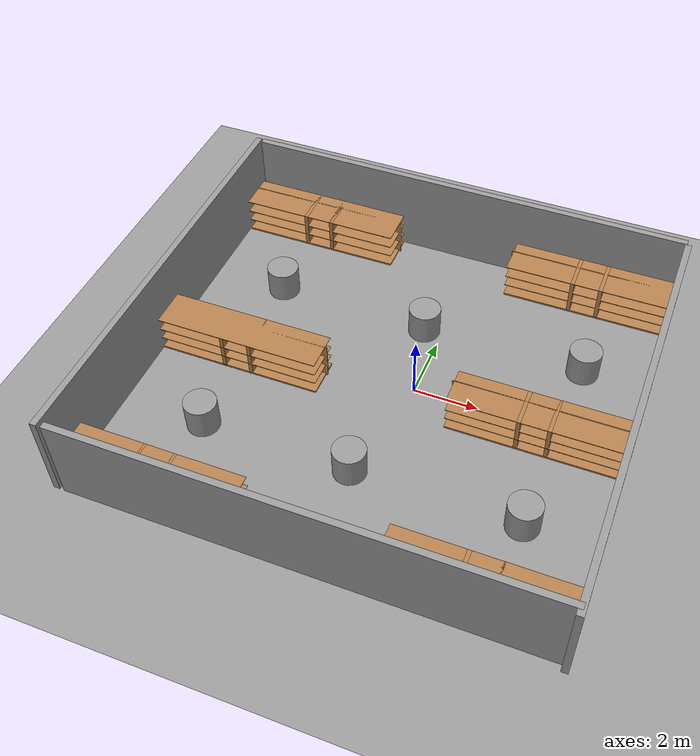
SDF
<sdf version="1.6">
 <world name="default">
  <light name="sun" type="directional">
   <pose>0 0 10 0 -0 0</pose>
   <diffuse>0.8 0.8 0.8 1</diffuse>
   <specular>0.2 0.2 0.2 1</specular>
   <attenuation>
    <range>1000</range>
    <constant>0.9</constant>
    <linear>0.01</linear>
    <quadratic>0.001</quadratic>
   </attenuation>
   <direction>0.5 0.1 -0.9</direction>
  </light>
  <scene><ambient>0.4 0.4 0.4 1</ambient><background>0.7 0.7 0.7 1</background><shadows>1</shadows></scene>
  <physics name="default_physics" default="0" type="ode">
   <max_step_size>0.01</max_step_size>
   <real_time_factor>1</real_time_factor>
   <real_time_update_rate>100</real_time_update_rate>
  </physics>
  <model name="ground_plane_0">
   <static>1</static>
   <link name="link">
    <collision name="collision">
     <geometry><plane><normal>0 0 1</normal><size>100 100</size></plane></geometry>
     <surface><friction><ode><mu>100</mu><mu2>50</mu2></ode></friction></surface>
    </collision>
    <visual name="visual">
     <cast_shadows>0</cast_shadows>
     <geometry><plane><normal>0 0 1</normal><size>100 100</size></plane></geometry>
     <material>
      <script><uri>file://media/materials/scripts/gazebo.material</uri><name>Gazebo/Grey</name></script>
     </material>
    </visual>
    <velocity_decay><linear>0</linear><angular>0</angular></velocity_decay>
   </link>
   <pose>0.497681 0 0 0 -0 0</pose>
  </model>
  <model name="unit_cylinder_1">
   <pose>-0.652064 -3.4888 0.49912 0 -0 0</pose>
   <link name="link">
    <inertial>
     <mass>1</mass>
     <inertia><ixx>1</ixx><ixy>0</ixy><ixz>0</ixz><iyy>1</iyy><iyz>0</iyz><izz>1</izz></inertia>
    </inertial>
    <collision name="collision">
     <geometry><cylinder><radius>0.5</radius><length>1</length></cylinder></geometry>
    </collision>
    <visual name="visual">
     <geometry><cylinder><radius>0.5</radius><length>1</length></cylinder></geometry>
     <material>
      <script><uri>file://media/materials/scripts/gazebo.material</uri><name>Gazebo/Grey</name></script>
     </material>
    </visual>
    <velocity_decay><linear>0</linear><angular>0</angular></velocity_decay>
   </link>
   <static>0</static>
  </model>
  <gravity>0 0 -9.8</gravity>
  <magnetic_field>6e-06 2.3e-05 -4.2e-05</magnetic_field>
  <atmosphere type="adiabatic"/>
  <spherical_coordinates>
   <surface_model>EARTH_WGS84</surface_model>
   <latitude_deg>0</latitude_deg>
   <longitude_deg>0</longitude_deg>
   <elevation>0</elevation>
   <heading_deg>0</heading_deg>
  </spherical_coordinates>
  <model name="unit_cylinder_1_clone">
   <pose>-0.580608 2.45625 0.49912 0 0 -0.000345</pose>
   <link name="link">
    <inertial>
     <mass>1</mass>
     <inertia><ixx>1</ixx><ixy>0</ixy><ixz>0</ixz><iyy>1</iyy><iyz>0</iyz><izz>1</izz></inertia>
    </inertial>
    <collision name="collision">
     <geometry><cylinder><radius>0.5</radius><length>1</length></cylinder></geometry>
    </collision>
    <visual name="visual">
     <geometry><cylinder><radius>0.5</radius><length>1</length></cylinder></geometry>
     <material>
      <script><uri>file://media/materials/scripts/gazebo.material</uri><name>Gazebo/Grey</name></script>
     </material>
    </visual>
    <velocity_decay><linear>0</linear><angular>0</angular></velocity_decay>
   </link>
   <static>0</static>
  </model>
  <model name="bookshelf1_clone_4">
   <link name="link">
    <pose>-5.30085 4.14714 0 0 -0 0</pose>
    <inertial>
     <mass>18.106</mass>
     <inertia><ixx>0</ixx><ixy>0</ixy><ixz>0</ixz><iyy>0</iyy><iyz>0</iyz><izz>0</izz></inertia>
    </inertial>
    <velocity_decay><linear>0</linear><angular>0</angular></velocity_decay>
    <visual name="visual1">
     <pose>0 0.005 0.6 0 -0 0</pose>
     <geometry><box><size>5.34173 0.029897 1.2</size></box></geometry>
     <material>
      <script><uri>file://media/materials/scripts/gazebo.material</uri><name>Gazebo/Wood</name></script>
      <ambient>1 1 1 1</ambient>
      <diffuse>1 1 1 1</diffuse>
      <specular>0.2 0.2 0.2 1</specular>
      <emissive>0 0 0 1</emissive>
      <shader type="vertex"><normal_map>__default__</normal_map></shader>
     </material>
    </visual>
    <visual name="visual2">
     <pose>0.45 -0.195 0.6 0 -0 0</pose>
     <geometry><box><size>0.118103 1.22649 1.2</size></box></geometry>
     <material>
      <script><uri>file://media/materials/scripts/gazebo.material</uri><name>Gazebo/Wood</name></script>
      <ambient>1 1 1 1</ambient>
      <diffuse>1 1 1 1</diffuse>
      <specular>0.2 0.2 0.2 1</specular>
      <emissive>0 0 0 1</emissive>
      <shader type="vertex"><normal_map>__default__</normal_map></shader>
     </material>
    </visual>
    <visual name="visual3">
     <pose>-0.45 -0.195 0.6 0 -0 0</pose>
     <geometry><box><size>0.118103 1.22649 1.2</size></box></geometry>
     <material>
      <script><uri>file://media/materials/scripts/gazebo.material</uri><name>Gazebo/Wood</name></script>
      <ambient>1 1 1 1</ambient>
      <diffuse>1 1 1 1</diffuse>
      <specular>0.2 0.2 0.2 1</specular>
      <emissive>0 0 0 1</emissive>
      <shader type="vertex"><normal_map>__default__</normal_map></shader>
     </material>
    </visual>
    <visual name="visual4">
     <pose>0 -0.195 0.03 0 -0 0</pose>
     <geometry><box><size>5.22302 1.22649 0.06</size></box></geometry>
     <material>
      <script><uri>file://media/materials/scripts/gazebo.material</uri><name>Gazebo/Wood</name></script>
      <ambient>1 1 1 1</ambient>
      <diffuse>1 1 1 1</diffuse>
      <specular>0.2 0.2 0.2 1</specular>
      <emissive>0 0 0 1</emissive>
      <shader type="vertex"><normal_map>__default__</normal_map></shader>
     </material>
    </visual>
    <visual name="visual5">
     <pose>0 -0.195 1.19 0 -0 0</pose>
     <geometry><box><size>5.22302 1.22649 0.02</size></box></geometry>
     <material>
      <script><uri>file://media/materials/scripts/gazebo.material</uri><name>Gazebo/Wood</name></script>
      <ambient>1 1 1 1</ambient>
      <diffuse>1 1 1 1</diffuse>
      <specular>0.2 0.2 0.2 1</specular>
      <emissive>0 0 0 1</emissive>
      <shader type="vertex"><normal_map>__default__</normal_map></shader>
     </material>
    </visual>
    <visual name="visual6">
     <pose>0 -0.195 0.43 0 -0 0</pose>
     <geometry><box><size>5.22302 1.22649 0.02</size></box></geometry>
     <material>
      <script><uri>file://media/materials/scripts/gazebo.material</uri><name>Gazebo/Wood</name></script>
      <ambient>1 1 1 1</ambient>
      <diffuse>1 1 1 1</diffuse>
      <specular>0.2 0.2 0.2 1</specular>
      <emissive>0 0 0 1</emissive>
      <shader type="vertex"><normal_map>__default__</normal_map></shader>
     </material>
    </visual>
    <visual name="visual7">
     <pose>0 -0.195 0.8 0 -0 0</pose>
     <geometry><box><size>5.22302 1.22649 0.02</size></box></geometry>
     <material>
      <script><uri>file://media/materials/scripts/gazebo.material</uri><name>Gazebo/Wood</name></script>
      <ambient>1 1 1 1</ambient>
      <diffuse>1 1 1 1</diffuse>
      <specular>0.2 0.2 0.2 1</specular>
      <emissive>0 0 0 1</emissive>
      <shader type="vertex"><normal_map>__default__</normal_map></shader>
     </material>
    </visual>
    <collision name="left_side">
     <pose>0.45 -0.195 0.6 0 -0 0</pose>
     <geometry><box><size>0.118103 1.22649 1.2</size></box></geometry>
     <surface>
      <friction>
       <ode><mu>1</mu><mu2>1</mu2><fdir1>0 0 0</fdir1><slip1>0</slip1><slip2>0</slip2></ode>
       <torsional>
        <coefficient>1</coefficient>
        <patch_radius>0</patch_radius>
        <surface_radius>0</surface_radius>
        <use_patch_radius>1</use_patch_radius>
        <ode><slip>0</slip></ode>
       </torsional>
      </friction>
      <bounce><restitution_coefficient>0</restitution_coefficient><threshold>1e+06</threshold></bounce>
      <contact>
       <collide_without_contact>0</collide_without_contact>
       <collide_without_contact_bitmask>1</collide_without_contact_bitmask>
       <collide_bitmask>1</collide_bitmask>
       <ode>
        <soft_cfm>0</soft_cfm>
        <soft_erp>0.2</soft_erp>
        <kp>1e+13</kp>
        <kd>1</kd>
        <max_vel>0.01</max_vel>
        <min_depth>0</min_depth>
       </ode>
       <bullet>
        <split_impulse>1</split_impulse>
        <split_impulse_penetration_threshold>-0.01</split_impulse_penetration_threshold>
        <soft_cfm>0</soft_cfm>
        <soft_erp>0.2</soft_erp>
        <kp>1e+13</kp>
        <kd>1</kd>
       </bullet>
      </contact>
     </surface>
    </collision>
    <collision name="back">
     <pose>0 0.005 0.6 0 -0 0</pose>
     <geometry><box><size>5.34173 0.029897 1.2</size></box></geometry>
     <surface>
      <friction>
       <ode><mu>1</mu><mu2>1</mu2><fdir1>0 0 0</fdir1><slip1>0</slip1><slip2>0</slip2></ode>
       <torsional>
        <coefficient>1</coefficient>
        <patch_radius>0</patch_radius>
        <surface_radius>0</surface_radius>
        <use_patch_radius>1</use_patch_radius>
        <ode><slip>0</slip></ode>
       </torsional>
      </friction>
      <bounce><restitution_coefficient>0</restitution_coefficient><threshold>1e+06</threshold></bounce>
      <contact>
       <collide_without_contact>0</collide_without_contact>
       <collide_without_contact_bitmask>1</collide_without_contact_bitmask>
       <collide_bitmask>1</collide_bitmask>
       <ode>
        <soft_cfm>0</soft_cfm>
        <soft_erp>0.2</soft_erp>
        <kp>1e+13</kp>
        <kd>1</kd>
        <max_vel>0.01</max_vel>
        <min_depth>0</min_depth>
       </ode>
       <bullet>
        <split_impulse>1</split_impulse>
        <split_impulse_penetration_threshold>-0.01</split_impulse_penetration_threshold>
        <soft_cfm>0</soft_cfm>
        <soft_erp>0.2</soft_erp>
        <kp>1e+13</kp>
        <kd>1</kd>
       </bullet>
      </contact>
     </surface>
    </collision>
    <collision name="right_side">
     <pose>-0.45 -0.195 0.6 0 -0 0</pose>
     <geometry><box><size>0.118103 1.22649 1.2</size></box></geometry>
     <surface>
      <friction>
       <ode><mu>1</mu><mu2>1</mu2><fdir1>0 0 0</fdir1><slip1>0</slip1><slip2>0</slip2></ode>
       <torsional>
        <coefficient>1</coefficient>
        <patch_radius>0</patch_radius>
        <surface_radius>0</surface_radius>
        <use_patch_radius>1</use_patch_radius>
        <ode><slip>0</slip></ode>
       </torsional>
      </friction>
      <bounce><restitution_coefficient>0</restitution_coefficient><threshold>1e+06</threshold></bounce>
      <contact>
       <collide_without_contact>0</collide_without_contact>
       <collide_without_contact_bitmask>1</collide_without_contact_bitmask>
       <collide_bitmask>1</collide_bitmask>
       <ode>
        <soft_cfm>0</soft_cfm>
        <soft_erp>0.2</soft_erp>
        <kp>1e+13</kp>
        <kd>1</kd>
        <max_vel>0.01</max_vel>
        <min_depth>0</min_depth>
       </ode>
       <bullet>
        <split_impulse>1</split_impulse>
        <split_impulse_penetration_threshold>-0.01</split_impulse_penetration_threshold>
        <soft_cfm>0</soft_cfm>
        <soft_erp>0.2</soft_erp>
        <kp>1e+13</kp>
        <kd>1</kd>
       </bullet>
      </contact>
     </surface>
    </collision>
    <collision name="bottom">
     <pose>0 -0.195 0.03 0 -0 0</pose>
     <geometry><box><size>5.22302 1.22649 0.06</size></box></geometry>
     <surface>
      <friction>
       <ode><mu>1</mu><mu2>1</mu2><fdir1>0 0 0</fdir1><slip1>0</slip1><slip2>0</slip2></ode>
       <torsional>
        <coefficient>1</coefficient>
        <patch_radius>0</patch_radius>
        <surface_radius>0</surface_radius>
        <use_patch_radius>1</use_patch_radius>
        <ode><slip>0</slip></ode>
       </torsional>
      </friction>
      <bounce><restitution_coefficient>0</restitution_coefficient><threshold>1e+06</threshold></bounce>
      <contact>
       <collide_without_contact>0</collide_without_contact>
       <collide_without_contact_bitmask>1</collide_without_contact_bitmask>
       <collide_bitmask>1</collide_bitmask>
       <ode>
        <soft_cfm>0</soft_cfm>
        <soft_erp>0.2</soft_erp>
        <kp>1e+13</kp>
        <kd>1</kd>
        <max_vel>0.01</max_vel>
        <min_depth>0</min_depth>
       </ode>
       <bullet>
        <split_impulse>1</split_impulse>
        <split_impulse_penetration_threshold>-0.01</split_impulse_penetration_threshold>
        <soft_cfm>0</soft_cfm>
        <soft_erp>0.2</soft_erp>
        <kp>1e+13</kp>
        <kd>1</kd>
       </bullet>
      </contact>
     </surface>
    </collision>
    <collision name="low_shelf">
     <pose>0 -0.195 0.43 0 -0 0</pose>
     <geometry><box><size>5.22302 1.22649 0.02</size></box></geometry>
     <surface>
      <friction>
       <ode><mu>1</mu><mu2>1</mu2><fdir1>0 0 0</fdir1><slip1>0</slip1><slip2>0</slip2></ode>
       <torsional>
        <coefficient>1</coefficient>
        <patch_radius>0</patch_radius>
        <surface_radius>0</surface_radius>
        <use_patch_radius>1</use_patch_radius>
        <ode><slip>0</slip></ode>
       </torsional>
      </friction>
      <bounce><restitution_coefficient>0</restitution_coefficient><threshold>1e+06</threshold></bounce>
      <contact>
       <collide_without_contact>0</collide_without_contact>
       <collide_without_contact_bitmask>1</collide_without_contact_bitmask>
       <collide_bitmask>1</collide_bitmask>
       <ode>
        <soft_cfm>0</soft_cfm>
        <soft_erp>0.2</soft_erp>
        <kp>1e+13</kp>
        <kd>1</kd>
        <max_vel>0.01</max_vel>
        <min_depth>0</min_depth>
       </ode>
       <bullet>
        <split_impulse>1</split_impulse>
        <split_impulse_penetration_threshold>-0.01</split_impulse_penetration_threshold>
        <soft_cfm>0</soft_cfm>
        <soft_erp>0.2</soft_erp>
        <kp>1e+13</kp>
        <kd>1</kd>
       </bullet>
      </contact>
     </surface>
    </collision>
    <collision name="top">
     <pose>0 -0.195 1.19 0 -0 0</pose>
     <geometry><box><size>5.22302 1.22649 0.02</size></box></geometry>
     <surface>
      <friction>
       <ode><mu>1</mu><mu2>1</mu2><fdir1>0 0 0</fdir1><slip1>0</slip1><slip2>0</slip2></ode>
       <torsional>
        <coefficient>1</coefficient>
        <patch_radius>0</patch_radius>
        <surface_radius>0</surface_radius>
        <use_patch_radius>1</use_patch_radius>
        <ode><slip>0</slip></ode>
       </torsional>
      </friction>
      <bounce><restitution_coefficient>0</restitution_coefficient><threshold>1e+06</threshold></bounce>
      <contact>
       <collide_without_contact>0</collide_without_contact>
       <collide_without_contact_bitmask>1</collide_without_contact_bitmask>
       <collide_bitmask>1</collide_bitmask>
       <ode>
        <soft_cfm>0</soft_cfm>
        <soft_erp>0.2</soft_erp>
        <kp>1e+13</kp>
        <kd>1</kd>
        <max_vel>0.01</max_vel>
        <min_depth>0</min_depth>
       </ode>
       <bullet>
        <split_impulse>1</split_impulse>
        <split_impulse_penetration_threshold>-0.01</split_impulse_penetration_threshold>
        <soft_cfm>0</soft_cfm>
        <soft_erp>0.2</soft_erp>
        <kp>1e+13</kp>
        <kd>1</kd>
       </bullet>
      </contact>
     </surface>
    </collision>
    <collision name="high_shelf">
     <pose>0 -0.195 0.8 0 -0 0</pose>
     <geometry><box><size>5.22302 1.22649 0.02</size></box></geometry>
     <surface>
      <friction>
       <ode><mu>1</mu><mu2>1</mu2><fdir1>0 0 0</fdir1><slip1>0</slip1><slip2>0</slip2></ode>
       <torsional>
        <coefficient>1</coefficient>
        <patch_radius>0</patch_radius>
        <surface_radius>0</surface_radius>
        <use_patch_radius>1</use_patch_radius>
        <ode><slip>0</slip></ode>
       </torsional>
      </friction>
      <bounce><restitution_coefficient>0</restitution_coefficient><threshold>1e+06</threshold></bounce>
      <contact>
       <collide_without_contact>0</collide_without_contact>
       <collide_without_contact_bitmask>1</collide_without_contact_bitmask>
       <collide_bitmask>1</collide_bitmask>
       <ode>
        <soft_cfm>0</soft_cfm>
        <soft_erp>0.2</soft_erp>
        <kp>1e+13</kp>
        <kd>1</kd>
        <max_vel>0.01</max_vel>
        <min_depth>0</min_depth>
       </ode>
       <bullet>
        <split_impulse>1</split_impulse>
        <split_impulse_penetration_threshold>-0.01</split_impulse_penetration_threshold>
        <soft_cfm>0</soft_cfm>
        <soft_erp>0.2</soft_erp>
        <kp>1e+13</kp>
        <kd>1</kd>
       </bullet>
      </contact>
     </surface>
    </collision>
   </link>
   <static>1</static>
   <pose>9.18802 1.64622 0 0 -0 0</pose>
  </model>
  <model name="bookshelf1_clone_4_clone">
   <link name="link">
    <pose>-5.30085 4.14714 0 0 -0 0</pose>
    <inertial>
     <mass>18.106</mass>
     <inertia><ixx>0</ixx><ixy>0</ixy><ixz>0</ixz><iyy>0</iyy><iyz>0</iyz><izz>0</izz></inertia>
    </inertial>
    <velocity_decay><linear>0</linear><angular>0</angular></velocity_decay>
    <visual name="visual1">
     <pose>0 0.005 0.6 0 -0 0</pose>
     <geometry><box><size>5.34173 0.029897 1.2</size></box></geometry>
     <material>
      <script><uri>file://media/materials/scripts/gazebo.material</uri><name>Gazebo/Wood</name></script>
      <ambient>1 1 1 1</ambient>
      <diffuse>1 1 1 1</diffuse>
      <specular>0.2 0.2 0.2 1</specular>
      <emissive>0 0 0 1</emissive>
      <shader type="vertex"><normal_map>__default__</normal_map></shader>
     </material>
    </visual>
    <visual name="visual2">
     <pose>0.45 -0.195 0.6 0 -0 0</pose>
     <geometry><box><size>0.118103 1.22649 1.2</size></box></geometry>
     <material>
      <script><uri>file://media/materials/scripts/gazebo.material</uri><name>Gazebo/Wood</name></script>
      <ambient>1 1 1 1</ambient>
      <diffuse>1 1 1 1</diffuse>
      <specular>0.2 0.2 0.2 1</specular>
      <emissive>0 0 0 1</emissive>
      <shader type="vertex"><normal_map>__default__</normal_map></shader>
     </material>
    </visual>
    <visual name="visual3">
     <pose>-0.45 -0.195 0.6 0 -0 0</pose>
     <geometry><box><size>0.118103 1.22649 1.2</size></box></geometry>
     <material>
      <script><uri>file://media/materials/scripts/gazebo.material</uri><name>Gazebo/Wood</name></script>
      <ambient>1 1 1 1</ambient>
      <diffuse>1 1 1 1</diffuse>
      <specular>0.2 0.2 0.2 1</specular>
      <emissive>0 0 0 1</emissive>
      <shader type="vertex"><normal_map>__default__</normal_map></shader>
     </material>
    </visual>
    <visual name="visual4">
     <pose>0 -0.195 0.03 0 -0 0</pose>
     <geometry><box><size>5.22302 1.22649 0.06</size></box></geometry>
     <material>
      <script><uri>file://media/materials/scripts/gazebo.material</uri><name>Gazebo/Wood</name></script>
      <ambient>1 1 1 1</ambient>
      <diffuse>1 1 1 1</diffuse>
      <specular>0.2 0.2 0.2 1</specular>
      <emissive>0 0 0 1</emissive>
      <shader type="vertex"><normal_map>__default__</normal_map></shader>
     </material>
    </visual>
    <visual name="visual5">
     <pose>0 -0.195 1.19 0 -0 0</pose>
     <geometry><box><size>5.22302 1.22649 0.02</size></box></geometry>
     <material>
      <script><uri>file://media/materials/scripts/gazebo.material</uri><name>Gazebo/Wood</name></script>
      <ambient>1 1 1 1</ambient>
      <diffuse>1 1 1 1</diffuse>
      <specular>0.2 0.2 0.2 1</specular>
      <emissive>0 0 0 1</emissive>
      <shader type="vertex"><normal_map>__default__</normal_map></shader>
     </material>
    </visual>
    <visual name="visual6">
     <pose>0 -0.195 0.43 0 -0 0</pose>
     <geometry><box><size>5.22302 1.22649 0.02</size></box></geometry>
     <material>
      <script><uri>file://media/materials/scripts/gazebo.material</uri><name>Gazebo/Wood</name></script>
      <ambient>1 1 1 1</ambient>
      <diffuse>1 1 1 1</diffuse>
      <specular>0.2 0.2 0.2 1</specular>
      <emissive>0 0 0 1</emissive>
      <shader type="vertex"><normal_map>__default__</normal_map></shader>
     </material>
    </visual>
    <visual name="visual7">
     <pose>0 -0.195 0.8 0 -0 0</pose>
     <geometry><box><size>5.22302 1.22649 0.02</size></box></geometry>
     <material>
      <script><uri>file://media/materials/scripts/gazebo.material</uri><name>Gazebo/Wood</name></script>
      <ambient>1 1 1 1</ambient>
      <diffuse>1 1 1 1</diffuse>
      <specular>0.2 0.2 0.2 1</specular>
      <emissive>0 0 0 1</emissive>
      <shader type="vertex"><normal_map>__default__</normal_map></shader>
     </material>
    </visual>
    <collision name="left_side">
     <pose>0.45 -0.195 0.6 0 -0 0</pose>
     <geometry><box><size>0.118103 1.22649 1.2</size></box></geometry>
     <surface>
      <friction>
       <ode><mu>1</mu><mu2>1</mu2><fdir1>0 0 0</fdir1><slip1>0</slip1><slip2>0</slip2></ode>
       <torsional>
        <coefficient>1</coefficient>
        <patch_radius>0</patch_radius>
        <surface_radius>0</surface_radius>
        <use_patch_radius>1</use_patch_radius>
        <ode><slip>0</slip></ode>
       </torsional>
      </friction>
      <bounce><restitution_coefficient>0</restitution_coefficient><threshold>1e+06</threshold></bounce>
      <contact>
       <collide_without_contact>0</collide_without_contact>
       <collide_without_contact_bitmask>1</collide_without_contact_bitmask>
       <collide_bitmask>1</collide_bitmask>
       <ode>
        <soft_cfm>0</soft_cfm>
        <soft_erp>0.2</soft_erp>
        <kp>1e+13</kp>
        <kd>1</kd>
        <max_vel>0.01</max_vel>
        <min_depth>0</min_depth>
       </ode>
       <bullet>
        <split_impulse>1</split_impulse>
        <split_impulse_penetration_threshold>-0.01</split_impulse_penetration_threshold>
        <soft_cfm>0</soft_cfm>
        <soft_erp>0.2</soft_erp>
        <kp>1e+13</kp>
        <kd>1</kd>
       </bullet>
      </contact>
     </surface>
    </collision>
    <collision name="back">
     <pose>0 0.005 0.6 0 -0 0</pose>
     <geometry><box><size>5.34173 0.029897 1.2</size></box></geometry>
     <surface>
      <friction>
       <ode><mu>1</mu><mu2>1</mu2><fdir1>0 0 0</fdir1><slip1>0</slip1><slip2>0</slip2></ode>
       <torsional>
        <coefficient>1</coefficient>
        <patch_radius>0</patch_radius>
        <surface_radius>0</surface_radius>
        <use_patch_radius>1</use_patch_radius>
        <ode><slip>0</slip></ode>
       </torsional>
      </friction>
      <bounce><restitution_coefficient>0</restitution_coefficient><threshold>1e+06</threshold></bounce>
      <contact>
       <collide_without_contact>0</collide_without_contact>
       <collide_without_contact_bitmask>1</collide_without_contact_bitmask>
       <collide_bitmask>1</collide_bitmask>
       <ode>
        <soft_cfm>0</soft_cfm>
        <soft_erp>0.2</soft_erp>
        <kp>1e+13</kp>
        <kd>1</kd>
        <max_vel>0.01</max_vel>
        <min_depth>0</min_depth>
       </ode>
       <bullet>
        <split_impulse>1</split_impulse>
        <split_impulse_penetration_threshold>-0.01</split_impulse_penetration_threshold>
        <soft_cfm>0</soft_cfm>
        <soft_erp>0.2</soft_erp>
        <kp>1e+13</kp>
        <kd>1</kd>
       </bullet>
      </contact>
     </surface>
    </collision>
    <collision name="right_side">
     <pose>-0.45 -0.195 0.6 0 -0 0</pose>
     <geometry><box><size>0.118103 1.22649 1.2</size></box></geometry>
     <surface>
      <friction>
       <ode><mu>1</mu><mu2>1</mu2><fdir1>0 0 0</fdir1><slip1>0</slip1><slip2>0</slip2></ode>
       <torsional>
        <coefficient>1</coefficient>
        <patch_radius>0</patch_radius>
        <surface_radius>0</surface_radius>
        <use_patch_radius>1</use_patch_radius>
        <ode><slip>0</slip></ode>
       </torsional>
      </friction>
      <bounce><restitution_coefficient>0</restitution_coefficient><threshold>1e+06</threshold></bounce>
      <contact>
       <collide_without_contact>0</collide_without_contact>
       <collide_without_contact_bitmask>1</collide_without_contact_bitmask>
       <collide_bitmask>1</collide_bitmask>
       <ode>
        <soft_cfm>0</soft_cfm>
        <soft_erp>0.2</soft_erp>
        <kp>1e+13</kp>
        <kd>1</kd>
        <max_vel>0.01</max_vel>
        <min_depth>0</min_depth>
       </ode>
       <bullet>
        <split_impulse>1</split_impulse>
        <split_impulse_penetration_threshold>-0.01</split_impulse_penetration_threshold>
        <soft_cfm>0</soft_cfm>
        <soft_erp>0.2</soft_erp>
        <kp>1e+13</kp>
        <kd>1</kd>
       </bullet>
      </contact>
     </surface>
    </collision>
    <collision name="bottom">
     <pose>0 -0.195 0.03 0 -0 0</pose>
     <geometry><box><size>5.22302 1.22649 0.06</size></box></geometry>
     <surface>
      <friction>
       <ode><mu>1</mu><mu2>1</mu2><fdir1>0 0 0</fdir1><slip1>0</slip1><slip2>0</slip2></ode>
       <torsional>
        <coefficient>1</coefficient>
        <patch_radius>0</patch_radius>
        <surface_radius>0</surface_radius>
        <use_patch_radius>1</use_patch_radius>
        <ode><slip>0</slip></ode>
       </torsional>
      </friction>
      <bounce><restitution_coefficient>0</restitution_coefficient><threshold>1e+06</threshold></bounce>
      <contact>
       <collide_without_contact>0</collide_without_contact>
       <collide_without_contact_bitmask>1</collide_without_contact_bitmask>
       <collide_bitmask>1</collide_bitmask>
       <ode>
        <soft_cfm>0</soft_cfm>
        <soft_erp>0.2</soft_erp>
        <kp>1e+13</kp>
        <kd>1</kd>
        <max_vel>0.01</max_vel>
        <min_depth>0</min_depth>
       </ode>
       <bullet>
        <split_impulse>1</split_impulse>
        <split_impulse_penetration_threshold>-0.01</split_impulse_penetration_threshold>
        <soft_cfm>0</soft_cfm>
        <soft_erp>0.2</soft_erp>
        <kp>1e+13</kp>
        <kd>1</kd>
       </bullet>
      </contact>
     </surface>
    </collision>
    <collision name="low_shelf">
     <pose>0 -0.195 0.43 0 -0 0</pose>
     <geometry><box><size>5.22302 1.22649 0.02</size></box></geometry>
     <surface>
      <friction>
       <ode><mu>1</mu><mu2>1</mu2><fdir1>0 0 0</fdir1><slip1>0</slip1><slip2>0</slip2></ode>
       <torsional>
        <coefficient>1</coefficient>
        <patch_radius>0</patch_radius>
        <surface_radius>0</surface_radius>
        <use_patch_radius>1</use_patch_radius>
        <ode><slip>0</slip></ode>
       </torsional>
      </friction>
      <bounce><restitution_coefficient>0</restitution_coefficient><threshold>1e+06</threshold></bounce>
      <contact>
       <collide_without_contact>0</collide_without_contact>
       <collide_without_contact_bitmask>1</collide_without_contact_bitmask>
       <collide_bitmask>1</collide_bitmask>
       <ode>
        <soft_cfm>0</soft_cfm>
        <soft_erp>0.2</soft_erp>
        <kp>1e+13</kp>
        <kd>1</kd>
        <max_vel>0.01</max_vel>
        <min_depth>0</min_depth>
       </ode>
       <bullet>
        <split_impulse>1</split_impulse>
        <split_impulse_penetration_threshold>-0.01</split_impulse_penetration_threshold>
        <soft_cfm>0</soft_cfm>
        <soft_erp>0.2</soft_erp>
        <kp>1e+13</kp>
        <kd>1</kd>
       </bullet>
      </contact>
     </surface>
    </collision>
    <collision name="top">
     <pose>0 -0.195 1.19 0 -0 0</pose>
     <geometry><box><size>5.22302 1.22649 0.02</size></box></geometry>
     <surface>
      <friction>
       <ode><mu>1</mu><mu2>1</mu2><fdir1>0 0 0</fdir1><slip1>0</slip1><slip2>0</slip2></ode>
       <torsional>
        <coefficient>1</coefficient>
        <patch_radius>0</patch_radius>
        <surface_radius>0</surface_radius>
        <use_patch_radius>1</use_patch_radius>
        <ode><slip>0</slip></ode>
       </torsional>
      </friction>
      <bounce><restitution_coefficient>0</restitution_coefficient><threshold>1e+06</threshold></bounce>
      <contact>
       <collide_without_contact>0</collide_without_contact>
       <collide_without_contact_bitmask>1</collide_without_contact_bitmask>
       <collide_bitmask>1</collide_bitmask>
       <ode>
        <soft_cfm>0</soft_cfm>
        <soft_erp>0.2</soft_erp>
        <kp>1e+13</kp>
        <kd>1</kd>
        <max_vel>0.01</max_vel>
        <min_depth>0</min_depth>
       </ode>
       <bullet>
        <split_impulse>1</split_impulse>
        <split_impulse_penetration_threshold>-0.01</split_impulse_penetration_threshold>
        <soft_cfm>0</soft_cfm>
        <soft_erp>0.2</soft_erp>
        <kp>1e+13</kp>
        <kd>1</kd>
       </bullet>
      </contact>
     </surface>
    </collision>
    <collision name="high_shelf">
     <pose>0 -0.195 0.8 0 -0 0</pose>
     <geometry><box><size>5.22302 1.22649 0.02</size></box></geometry>
     <surface>
      <friction>
       <ode><mu>1</mu><mu2>1</mu2><fdir1>0 0 0</fdir1><slip1>0</slip1><slip2>0</slip2></ode>
       <torsional>
        <coefficient>1</coefficient>
        <patch_radius>0</patch_radius>
        <surface_radius>0</surface_radius>
        <use_patch_radius>1</use_patch_radius>
        <ode><slip>0</slip></ode>
       </torsional>
      </friction>
      <bounce><restitution_coefficient>0</restitution_coefficient><threshold>1e+06</threshold></bounce>
      <contact>
       <collide_without_contact>0</collide_without_contact>
       <collide_without_contact_bitmask>1</collide_without_contact_bitmask>
       <collide_bitmask>1</collide_bitmask>
       <ode>
        <soft_cfm>0</soft_cfm>
        <soft_erp>0.2</soft_erp>
        <kp>1e+13</kp>
        <kd>1</kd>
        <max_vel>0.01</max_vel>
        <min_depth>0</min_depth>
       </ode>
       <bullet>
        <split_impulse>1</split_impulse>
        <split_impulse_penetration_threshold>-0.01</split_impulse_penetration_threshold>
        <soft_cfm>0</soft_cfm>
        <soft_erp>0.2</soft_erp>
        <kp>1e+13</kp>
        <kd>1</kd>
       </bullet>
      </contact>
     </surface>
    </collision>
   </link>
   <static>1</static>
   <pose>9.20317 -4.37233 0 0 -0 0</pose>
  </model>
  <model name="bookshelf1_clone_4_clone_0">
   <link name="link">
    <pose>-5.30085 4.14714 0 0 -0 0</pose>
    <inertial>
     <mass>18.106</mass>
     <inertia><ixx>0</ixx><ixy>0</ixy><ixz>0</ixz><iyy>0</iyy><iyz>0</iyz><izz>0</izz></inertia>
    </inertial>
    <velocity_decay><linear>0</linear><angular>0</angular></velocity_decay>
    <visual name="visual1">
     <pose>0 0.005 0.6 0 -0 0</pose>
     <geometry><box><size>5.34173 0.029897 1.2</size></box></geometry>
     <material>
      <script><uri>file://media/materials/scripts/gazebo.material</uri><name>Gazebo/Wood</name></script>
      <ambient>1 1 1 1</ambient>
      <diffuse>1 1 1 1</diffuse>
      <specular>0.2 0.2 0.2 1</specular>
      <emissive>0 0 0 1</emissive>
      <shader type="vertex"><normal_map>__default__</normal_map></shader>
     </material>
    </visual>
    <visual name="visual2">
     <pose>0.45 -0.195 0.6 0 -0 0</pose>
     <geometry><box><size>0.118103 1.22649 1.2</size></box></geometry>
     <material>
      <script><uri>file://media/materials/scripts/gazebo.material</uri><name>Gazebo/Wood</name></script>
      <ambient>1 1 1 1</ambient>
      <diffuse>1 1 1 1</diffuse>
      <specular>0.2 0.2 0.2 1</specular>
      <emissive>0 0 0 1</emissive>
      <shader type="vertex"><normal_map>__default__</normal_map></shader>
     </material>
    </visual>
    <visual name="visual3">
     <pose>-0.45 -0.195 0.6 0 -0 0</pose>
     <geometry><box><size>0.118103 1.22649 1.2</size></box></geometry>
     <material>
      <script><uri>file://media/materials/scripts/gazebo.material</uri><name>Gazebo/Wood</name></script>
      <ambient>1 1 1 1</ambient>
      <diffuse>1 1 1 1</diffuse>
      <specular>0.2 0.2 0.2 1</specular>
      <emissive>0 0 0 1</emissive>
      <shader type="vertex"><normal_map>__default__</normal_map></shader>
     </material>
    </visual>
    <visual name="visual4">
     <pose>0 -0.195 0.03 0 -0 0</pose>
     <geometry><box><size>5.22302 1.22649 0.06</size></box></geometry>
     <material>
      <script><uri>file://media/materials/scripts/gazebo.material</uri><name>Gazebo/Wood</name></script>
      <ambient>1 1 1 1</ambient>
      <diffuse>1 1 1 1</diffuse>
      <specular>0.2 0.2 0.2 1</specular>
      <emissive>0 0 0 1</emissive>
      <shader type="vertex"><normal_map>__default__</normal_map></shader>
     </material>
    </visual>
    <visual name="visual5">
     <pose>0 -0.195 1.19 0 -0 0</pose>
     <geometry><box><size>5.22302 1.22649 0.02</size></box></geometry>
     <material>
      <script><uri>file://media/materials/scripts/gazebo.material</uri><name>Gazebo/Wood</name></script>
      <ambient>1 1 1 1</ambient>
      <diffuse>1 1 1 1</diffuse>
      <specular>0.2 0.2 0.2 1</specular>
      <emissive>0 0 0 1</emissive>
      <shader type="vertex"><normal_map>__default__</normal_map></shader>
     </material>
    </visual>
    <visual name="visual6">
     <pose>0 -0.195 0.43 0 -0 0</pose>
     <geometry><box><size>5.22302 1.22649 0.02</size></box></geometry>
     <material>
      <script><uri>file://media/materials/scripts/gazebo.material</uri><name>Gazebo/Wood</name></script>
      <ambient>1 1 1 1</ambient>
      <diffuse>1 1 1 1</diffuse>
      <specular>0.2 0.2 0.2 1</specular>
      <emissive>0 0 0 1</emissive>
      <shader type="vertex"><normal_map>__default__</normal_map></shader>
     </material>
    </visual>
    <visual name="visual7">
     <pose>0 -0.195 0.8 0 -0 0</pose>
     <geometry><box><size>5.22302 1.22649 0.02</size></box></geometry>
     <material>
      <script><uri>file://media/materials/scripts/gazebo.material</uri><name>Gazebo/Wood</name></script>
      <ambient>1 1 1 1</ambient>
      <diffuse>1 1 1 1</diffuse>
      <specular>0.2 0.2 0.2 1</specular>
      <emissive>0 0 0 1</emissive>
      <shader type="vertex"><normal_map>__default__</normal_map></shader>
     </material>
    </visual>
    <collision name="left_side">
     <pose>0.45 -0.195 0.6 0 -0 0</pose>
     <geometry><box><size>0.118103 1.22649 1.2</size></box></geometry>
     <surface>
      <friction>
       <ode><mu>1</mu><mu2>1</mu2><fdir1>0 0 0</fdir1><slip1>0</slip1><slip2>0</slip2></ode>
       <torsional>
        <coefficient>1</coefficient>
        <patch_radius>0</patch_radius>
        <surface_radius>0</surface_radius>
        <use_patch_radius>1</use_patch_radius>
        <ode><slip>0</slip></ode>
       </torsional>
      </friction>
      <bounce><restitution_coefficient>0</restitution_coefficient><threshold>1e+06</threshold></bounce>
      <contact>
       <collide_without_contact>0</collide_without_contact>
       <collide_without_contact_bitmask>1</collide_without_contact_bitmask>
       <collide_bitmask>1</collide_bitmask>
       <ode>
        <soft_cfm>0</soft_cfm>
        <soft_erp>0.2</soft_erp>
        <kp>1e+13</kp>
        <kd>1</kd>
        <max_vel>0.01</max_vel>
        <min_depth>0</min_depth>
       </ode>
       <bullet>
        <split_impulse>1</split_impulse>
        <split_impulse_penetration_threshold>-0.01</split_impulse_penetration_threshold>
        <soft_cfm>0</soft_cfm>
        <soft_erp>0.2</soft_erp>
        <kp>1e+13</kp>
        <kd>1</kd>
       </bullet>
      </contact>
     </surface>
    </collision>
    <collision name="back">
     <pose>0 0.005 0.6 0 -0 0</pose>
     <geometry><box><size>5.34173 0.029897 1.2</size></box></geometry>
     <surface>
      <friction>
       <ode><mu>1</mu><mu2>1</mu2><fdir1>0 0 0</fdir1><slip1>0</slip1><slip2>0</slip2></ode>
       <torsional>
        <coefficient>1</coefficient>
        <patch_radius>0</patch_radius>
        <surface_radius>0</surface_radius>
        <use_patch_radius>1</use_patch_radius>
        <ode><slip>0</slip></ode>
       </torsional>
      </friction>
      <bounce><restitution_coefficient>0</restitution_coefficient><threshold>1e+06</threshold></bounce>
      <contact>
       <collide_without_contact>0</collide_without_contact>
       <collide_without_contact_bitmask>1</collide_without_contact_bitmask>
       <collide_bitmask>1</collide_bitmask>
       <ode>
        <soft_cfm>0</soft_cfm>
        <soft_erp>0.2</soft_erp>
        <kp>1e+13</kp>
        <kd>1</kd>
        <max_vel>0.01</max_vel>
        <min_depth>0</min_depth>
       </ode>
       <bullet>
        <split_impulse>1</split_impulse>
        <split_impulse_penetration_threshold>-0.01</split_impulse_penetration_threshold>
        <soft_cfm>0</soft_cfm>
        <soft_erp>0.2</soft_erp>
        <kp>1e+13</kp>
        <kd>1</kd>
       </bullet>
      </contact>
     </surface>
    </collision>
    <collision name="right_side">
     <pose>-0.45 -0.195 0.6 0 -0 0</pose>
     <geometry><box><size>0.118103 1.22649 1.2</size></box></geometry>
     <surface>
      <friction>
       <ode><mu>1</mu><mu2>1</mu2><fdir1>0 0 0</fdir1><slip1>0</slip1><slip2>0</slip2></ode>
       <torsional>
        <coefficient>1</coefficient>
        <patch_radius>0</patch_radius>
        <surface_radius>0</surface_radius>
        <use_patch_radius>1</use_patch_radius>
        <ode><slip>0</slip></ode>
       </torsional>
      </friction>
      <bounce><restitution_coefficient>0</restitution_coefficient><threshold>1e+06</threshold></bounce>
      <contact>
       <collide_without_contact>0</collide_without_contact>
       <collide_without_contact_bitmask>1</collide_without_contact_bitmask>
       <collide_bitmask>1</collide_bitmask>
       <ode>
        <soft_cfm>0</soft_cfm>
        <soft_erp>0.2</soft_erp>
        <kp>1e+13</kp>
        <kd>1</kd>
        <max_vel>0.01</max_vel>
        <min_depth>0</min_depth>
       </ode>
       <bullet>
        <split_impulse>1</split_impulse>
        <split_impulse_penetration_threshold>-0.01</split_impulse_penetration_threshold>
        <soft_cfm>0</soft_cfm>
        <soft_erp>0.2</soft_erp>
        <kp>1e+13</kp>
        <kd>1</kd>
       </bullet>
      </contact>
     </surface>
    </collision>
    <collision name="bottom">
     <pose>0 -0.195 0.03 0 -0 0</pose>
     <geometry><box><size>5.22302 1.22649 0.06</size></box></geometry>
     <surface>
      <friction>
       <ode><mu>1</mu><mu2>1</mu2><fdir1>0 0 0</fdir1><slip1>0</slip1><slip2>0</slip2></ode>
       <torsional>
        <coefficient>1</coefficient>
        <patch_radius>0</patch_radius>
        <surface_radius>0</surface_radius>
        <use_patch_radius>1</use_patch_radius>
        <ode><slip>0</slip></ode>
       </torsional>
      </friction>
      <bounce><restitution_coefficient>0</restitution_coefficient><threshold>1e+06</threshold></bounce>
      <contact>
       <collide_without_contact>0</collide_without_contact>
       <collide_without_contact_bitmask>1</collide_without_contact_bitmask>
       <collide_bitmask>1</collide_bitmask>
       <ode>
        <soft_cfm>0</soft_cfm>
        <soft_erp>0.2</soft_erp>
        <kp>1e+13</kp>
        <kd>1</kd>
        <max_vel>0.01</max_vel>
        <min_depth>0</min_depth>
       </ode>
       <bullet>
        <split_impulse>1</split_impulse>
        <split_impulse_penetration_threshold>-0.01</split_impulse_penetration_threshold>
        <soft_cfm>0</soft_cfm>
        <soft_erp>0.2</soft_erp>
        <kp>1e+13</kp>
        <kd>1</kd>
       </bullet>
      </contact>
     </surface>
    </collision>
    <collision name="low_shelf">
     <pose>0 -0.195 0.43 0 -0 0</pose>
     <geometry><box><size>5.22302 1.22649 0.02</size></box></geometry>
     <surface>
      <friction>
       <ode><mu>1</mu><mu2>1</mu2><fdir1>0 0 0</fdir1><slip1>0</slip1><slip2>0</slip2></ode>
       <torsional>
        <coefficient>1</coefficient>
        <patch_radius>0</patch_radius>
        <surface_radius>0</surface_radius>
        <use_patch_radius>1</use_patch_radius>
        <ode><slip>0</slip></ode>
       </torsional>
      </friction>
      <bounce><restitution_coefficient>0</restitution_coefficient><threshold>1e+06</threshold></bounce>
      <contact>
       <collide_without_contact>0</collide_without_contact>
       <collide_without_contact_bitmask>1</collide_without_contact_bitmask>
       <collide_bitmask>1</collide_bitmask>
       <ode>
        <soft_cfm>0</soft_cfm>
        <soft_erp>0.2</soft_erp>
        <kp>1e+13</kp>
        <kd>1</kd>
        <max_vel>0.01</max_vel>
        <min_depth>0</min_depth>
       </ode>
       <bullet>
        <split_impulse>1</split_impulse>
        <split_impulse_penetration_threshold>-0.01</split_impulse_penetration_threshold>
        <soft_cfm>0</soft_cfm>
        <soft_erp>0.2</soft_erp>
        <kp>1e+13</kp>
        <kd>1</kd>
       </bullet>
      </contact>
     </surface>
    </collision>
    <collision name="top">
     <pose>0 -0.195 1.19 0 -0 0</pose>
     <geometry><box><size>5.22302 1.22649 0.02</size></box></geometry>
     <surface>
      <friction>
       <ode><mu>1</mu><mu2>1</mu2><fdir1>0 0 0</fdir1><slip1>0</slip1><slip2>0</slip2></ode>
       <torsional>
        <coefficient>1</coefficient>
        <patch_radius>0</patch_radius>
        <surface_radius>0</surface_radius>
        <use_patch_radius>1</use_patch_radius>
        <ode><slip>0</slip></ode>
       </torsional>
      </friction>
      <bounce><restitution_coefficient>0</restitution_coefficient><threshold>1e+06</threshold></bounce>
      <contact>
       <collide_without_contact>0</collide_without_contact>
       <collide_without_contact_bitmask>1</collide_without_contact_bitmask>
       <collide_bitmask>1</collide_bitmask>
       <ode>
        <soft_cfm>0</soft_cfm>
        <soft_erp>0.2</soft_erp>
        <kp>1e+13</kp>
        <kd>1</kd>
        <max_vel>0.01</max_vel>
        <min_depth>0</min_depth>
       </ode>
       <bullet>
        <split_impulse>1</split_impulse>
        <split_impulse_penetration_threshold>-0.01</split_impulse_penetration_threshold>
        <soft_cfm>0</soft_cfm>
        <soft_erp>0.2</soft_erp>
        <kp>1e+13</kp>
        <kd>1</kd>
       </bullet>
      </contact>
     </surface>
    </collision>
    <collision name="high_shelf">
     <pose>0 -0.195 0.8 0 -0 0</pose>
     <geometry><box><size>5.22302 1.22649 0.02</size></box></geometry>
     <surface>
      <friction>
       <ode><mu>1</mu><mu2>1</mu2><fdir1>0 0 0</fdir1><slip1>0</slip1><slip2>0</slip2></ode>
       <torsional>
        <coefficient>1</coefficient>
        <patch_radius>0</patch_radius>
        <surface_radius>0</surface_radius>
        <use_patch_radius>1</use_patch_radius>
        <ode><slip>0</slip></ode>
       </torsional>
      </friction>
      <bounce><restitution_coefficient>0</restitution_coefficient><threshold>1e+06</threshold></bounce>
      <contact>
       <collide_without_contact>0</collide_without_contact>
       <collide_without_contact_bitmask>1</collide_without_contact_bitmask>
       <collide_bitmask>1</collide_bitmask>
       <ode>
        <soft_cfm>0</soft_cfm>
        <soft_erp>0.2</soft_erp>
        <kp>1e+13</kp>
        <kd>1</kd>
        <max_vel>0.01</max_vel>
        <min_depth>0</min_depth>
       </ode>
       <bullet>
        <split_impulse>1</split_impulse>
        <split_impulse_penetration_threshold>-0.01</split_impulse_penetration_threshold>
        <soft_cfm>0</soft_cfm>
        <soft_erp>0.2</soft_erp>
        <kp>1e+13</kp>
        <kd>1</kd>
       </bullet>
      </contact>
     </surface>
    </collision>
   </link>
   <static>1</static>
   <pose>9.24091 -10.0132 0 0 -0 0</pose>
  </model>
  <model name="bookshelf1_clone_4_clone_1">
   <link name="link">
    <pose>-5.30085 4.14714 0 0 -0 0</pose>
    <inertial>
     <mass>18.106</mass>
     <inertia><ixx>0</ixx><ixy>0</ixy><ixz>0</ixz><iyy>0</iyy><iyz>0</iyz><izz>0</izz></inertia>
    </inertial>
    <velocity_decay><linear>0</linear><angular>0</angular></velocity_decay>
    <visual name="visual1">
     <pose>0 0.005 0.6 0 -0 0</pose>
     <geometry><box><size>5.34173 0.029897 1.2</size></box></geometry>
     <material>
      <script><uri>file://media/materials/scripts/gazebo.material</uri><name>Gazebo/Wood</name></script>
      <ambient>1 1 1 1</ambient>
      <diffuse>1 1 1 1</diffuse>
      <specular>0.2 0.2 0.2 1</specular>
      <emissive>0 0 0 1</emissive>
      <shader type="vertex"><normal_map>__default__</normal_map></shader>
     </material>
    </visual>
    <visual name="visual2">
     <pose>0.45 -0.195 0.6 0 -0 0</pose>
     <geometry><box><size>0.118103 1.22649 1.2</size></box></geometry>
     <material>
      <script><uri>file://media/materials/scripts/gazebo.material</uri><name>Gazebo/Wood</name></script>
      <ambient>1 1 1 1</ambient>
      <diffuse>1 1 1 1</diffuse>
      <specular>0.2 0.2 0.2 1</specular>
      <emissive>0 0 0 1</emissive>
      <shader type="vertex"><normal_map>__default__</normal_map></shader>
     </material>
    </visual>
    <visual name="visual3">
     <pose>-0.45 -0.195 0.6 0 -0 0</pose>
     <geometry><box><size>0.118103 1.22649 1.2</size></box></geometry>
     <material>
      <script><uri>file://media/materials/scripts/gazebo.material</uri><name>Gazebo/Wood</name></script>
      <ambient>1 1 1 1</ambient>
      <diffuse>1 1 1 1</diffuse>
      <specular>0.2 0.2 0.2 1</specular>
      <emissive>0 0 0 1</emissive>
      <shader type="vertex"><normal_map>__default__</normal_map></shader>
     </material>
    </visual>
    <visual name="visual4">
     <pose>0 -0.195 0.03 0 -0 0</pose>
     <geometry><box><size>5.22302 1.22649 0.06</size></box></geometry>
     <material>
      <script><uri>file://media/materials/scripts/gazebo.material</uri><name>Gazebo/Wood</name></script>
      <ambient>1 1 1 1</ambient>
      <diffuse>1 1 1 1</diffuse>
      <specular>0.2 0.2 0.2 1</specular>
      <emissive>0 0 0 1</emissive>
      <shader type="vertex"><normal_map>__default__</normal_map></shader>
     </material>
    </visual>
    <visual name="visual5">
     <pose>0 -0.195 1.19 0 -0 0</pose>
     <geometry><box><size>5.22302 1.22649 0.02</size></box></geometry>
     <material>
      <script><uri>file://media/materials/scripts/gazebo.material</uri><name>Gazebo/Wood</name></script>
      <ambient>1 1 1 1</ambient>
      <diffuse>1 1 1 1</diffuse>
      <specular>0.2 0.2 0.2 1</specular>
      <emissive>0 0 0 1</emissive>
      <shader type="vertex"><normal_map>__default__</normal_map></shader>
     </material>
    </visual>
    <visual name="visual6">
     <pose>0 -0.195 0.43 0 -0 0</pose>
     <geometry><box><size>5.22302 1.22649 0.02</size></box></geometry>
     <material>
      <script><uri>file://media/materials/scripts/gazebo.material</uri><name>Gazebo/Wood</name></script>
      <ambient>1 1 1 1</ambient>
      <diffuse>1 1 1 1</diffuse>
      <specular>0.2 0.2 0.2 1</specular>
      <emissive>0 0 0 1</emissive>
      <shader type="vertex"><normal_map>__default__</normal_map></shader>
     </material>
    </visual>
    <visual name="visual7">
     <pose>0 -0.195 0.8 0 -0 0</pose>
     <geometry><box><size>5.22302 1.22649 0.02</size></box></geometry>
     <material>
      <script><uri>file://media/materials/scripts/gazebo.material</uri><name>Gazebo/Wood</name></script>
      <ambient>1 1 1 1</ambient>
      <diffuse>1 1 1 1</diffuse>
      <specular>0.2 0.2 0.2 1</specular>
      <emissive>0 0 0 1</emissive>
      <shader type="vertex"><normal_map>__default__</normal_map></shader>
     </material>
    </visual>
    <collision name="left_side">
     <pose>0.45 -0.195 0.6 0 -0 0</pose>
     <geometry><box><size>0.118103 1.22649 1.2</size></box></geometry>
     <surface>
      <friction>
       <ode><mu>1</mu><mu2>1</mu2><fdir1>0 0 0</fdir1><slip1>0</slip1><slip2>0</slip2></ode>
       <torsional>
        <coefficient>1</coefficient>
        <patch_radius>0</patch_radius>
        <surface_radius>0</surface_radius>
        <use_patch_radius>1</use_patch_radius>
        <ode><slip>0</slip></ode>
       </torsional>
      </friction>
      <bounce><restitution_coefficient>0</restitution_coefficient><threshold>1e+06</threshold></bounce>
      <contact>
       <collide_without_contact>0</collide_without_contact>
       <collide_without_contact_bitmask>1</collide_without_contact_bitmask>
       <collide_bitmask>1</collide_bitmask>
       <ode>
        <soft_cfm>0</soft_cfm>
        <soft_erp>0.2</soft_erp>
        <kp>1e+13</kp>
        <kd>1</kd>
        <max_vel>0.01</max_vel>
        <min_depth>0</min_depth>
       </ode>
       <bullet>
        <split_impulse>1</split_impulse>
        <split_impulse_penetration_threshold>-0.01</split_impulse_penetration_threshold>
        <soft_cfm>0</soft_cfm>
        <soft_erp>0.2</soft_erp>
        <kp>1e+13</kp>
        <kd>1</kd>
       </bullet>
      </contact>
     </surface>
    </collision>
    <collision name="back">
     <pose>0 0.005 0.6 0 -0 0</pose>
     <geometry><box><size>5.34173 0.029897 1.2</size></box></geometry>
     <surface>
      <friction>
       <ode><mu>1</mu><mu2>1</mu2><fdir1>0 0 0</fdir1><slip1>0</slip1><slip2>0</slip2></ode>
       <torsional>
        <coefficient>1</coefficient>
        <patch_radius>0</patch_radius>
        <surface_radius>0</surface_radius>
        <use_patch_radius>1</use_patch_radius>
        <ode><slip>0</slip></ode>
       </torsional>
      </friction>
      <bounce><restitution_coefficient>0</restitution_coefficient><threshold>1e+06</threshold></bounce>
      <contact>
       <collide_without_contact>0</collide_without_contact>
       <collide_without_contact_bitmask>1</collide_without_contact_bitmask>
       <collide_bitmask>1</collide_bitmask>
       <ode>
        <soft_cfm>0</soft_cfm>
        <soft_erp>0.2</soft_erp>
        <kp>1e+13</kp>
        <kd>1</kd>
        <max_vel>0.01</max_vel>
        <min_depth>0</min_depth>
       </ode>
       <bullet>
        <split_impulse>1</split_impulse>
        <split_impulse_penetration_threshold>-0.01</split_impulse_penetration_threshold>
        <soft_cfm>0</soft_cfm>
        <soft_erp>0.2</soft_erp>
        <kp>1e+13</kp>
        <kd>1</kd>
       </bullet>
      </contact>
     </surface>
    </collision>
    <collision name="right_side">
     <pose>-0.45 -0.195 0.6 0 -0 0</pose>
     <geometry><box><size>0.118103 1.22649 1.2</size></box></geometry>
     <surface>
      <friction>
       <ode><mu>1</mu><mu2>1</mu2><fdir1>0 0 0</fdir1><slip1>0</slip1><slip2>0</slip2></ode>
       <torsional>
        <coefficient>1</coefficient>
        <patch_radius>0</patch_radius>
        <surface_radius>0</surface_radius>
        <use_patch_radius>1</use_patch_radius>
        <ode><slip>0</slip></ode>
       </torsional>
      </friction>
      <bounce><restitution_coefficient>0</restitution_coefficient><threshold>1e+06</threshold></bounce>
      <contact>
       <collide_without_contact>0</collide_without_contact>
       <collide_without_contact_bitmask>1</collide_without_contact_bitmask>
       <collide_bitmask>1</collide_bitmask>
       <ode>
        <soft_cfm>0</soft_cfm>
        <soft_erp>0.2</soft_erp>
        <kp>1e+13</kp>
        <kd>1</kd>
        <max_vel>0.01</max_vel>
        <min_depth>0</min_depth>
       </ode>
       <bullet>
        <split_impulse>1</split_impulse>
        <split_impulse_penetration_threshold>-0.01</split_impulse_penetration_threshold>
        <soft_cfm>0</soft_cfm>
        <soft_erp>0.2</soft_erp>
        <kp>1e+13</kp>
        <kd>1</kd>
       </bullet>
      </contact>
     </surface>
    </collision>
    <collision name="bottom">
     <pose>0 -0.195 0.03 0 -0 0</pose>
     <geometry><box><size>5.22302 1.22649 0.06</size></box></geometry>
     <surface>
      <friction>
       <ode><mu>1</mu><mu2>1</mu2><fdir1>0 0 0</fdir1><slip1>0</slip1><slip2>0</slip2></ode>
       <torsional>
        <coefficient>1</coefficient>
        <patch_radius>0</patch_radius>
        <surface_radius>0</surface_radius>
        <use_patch_radius>1</use_patch_radius>
        <ode><slip>0</slip></ode>
       </torsional>
      </friction>
      <bounce><restitution_coefficient>0</restitution_coefficient><threshold>1e+06</threshold></bounce>
      <contact>
       <collide_without_contact>0</collide_without_contact>
       <collide_without_contact_bitmask>1</collide_without_contact_bitmask>
       <collide_bitmask>1</collide_bitmask>
       <ode>
        <soft_cfm>0</soft_cfm>
        <soft_erp>0.2</soft_erp>
        <kp>1e+13</kp>
        <kd>1</kd>
        <max_vel>0.01</max_vel>
        <min_depth>0</min_depth>
       </ode>
       <bullet>
        <split_impulse>1</split_impulse>
        <split_impulse_penetration_threshold>-0.01</split_impulse_penetration_threshold>
        <soft_cfm>0</soft_cfm>
        <soft_erp>0.2</soft_erp>
        <kp>1e+13</kp>
        <kd>1</kd>
       </bullet>
      </contact>
     </surface>
    </collision>
    <collision name="low_shelf">
     <pose>0 -0.195 0.43 0 -0 0</pose>
     <geometry><box><size>5.22302 1.22649 0.02</size></box></geometry>
     <surface>
      <friction>
       <ode><mu>1</mu><mu2>1</mu2><fdir1>0 0 0</fdir1><slip1>0</slip1><slip2>0</slip2></ode>
       <torsional>
        <coefficient>1</coefficient>
        <patch_radius>0</patch_radius>
        <surface_radius>0</surface_radius>
        <use_patch_radius>1</use_patch_radius>
        <ode><slip>0</slip></ode>
       </torsional>
      </friction>
      <bounce><restitution_coefficient>0</restitution_coefficient><threshold>1e+06</threshold></bounce>
      <contact>
       <collide_without_contact>0</collide_without_contact>
       <collide_without_contact_bitmask>1</collide_without_contact_bitmask>
       <collide_bitmask>1</collide_bitmask>
       <ode>
        <soft_cfm>0</soft_cfm>
        <soft_erp>0.2</soft_erp>
        <kp>1e+13</kp>
        <kd>1</kd>
        <max_vel>0.01</max_vel>
        <min_depth>0</min_depth>
       </ode>
       <bullet>
        <split_impulse>1</split_impulse>
        <split_impulse_penetration_threshold>-0.01</split_impulse_penetration_threshold>
        <soft_cfm>0</soft_cfm>
        <soft_erp>0.2</soft_erp>
        <kp>1e+13</kp>
        <kd>1</kd>
       </bullet>
      </contact>
     </surface>
    </collision>
    <collision name="top">
     <pose>0 -0.195 1.19 0 -0 0</pose>
     <geometry><box><size>5.22302 1.22649 0.02</size></box></geometry>
     <surface>
      <friction>
       <ode><mu>1</mu><mu2>1</mu2><fdir1>0 0 0</fdir1><slip1>0</slip1><slip2>0</slip2></ode>
       <torsional>
        <coefficient>1</coefficient>
        <patch_radius>0</patch_radius>
        <surface_radius>0</surface_radius>
        <use_patch_radius>1</use_patch_radius>
        <ode><slip>0</slip></ode>
       </torsional>
      </friction>
      <bounce><restitution_coefficient>0</restitution_coefficient><threshold>1e+06</threshold></bounce>
      <contact>
       <collide_without_contact>0</collide_without_contact>
       <collide_without_contact_bitmask>1</collide_without_contact_bitmask>
       <collide_bitmask>1</collide_bitmask>
       <ode>
        <soft_cfm>0</soft_cfm>
        <soft_erp>0.2</soft_erp>
        <kp>1e+13</kp>
        <kd>1</kd>
        <max_vel>0.01</max_vel>
        <min_depth>0</min_depth>
       </ode>
       <bullet>
        <split_impulse>1</split_impulse>
        <split_impulse_penetration_threshold>-0.01</split_impulse_penetration_threshold>
        <soft_cfm>0</soft_cfm>
        <soft_erp>0.2</soft_erp>
        <kp>1e+13</kp>
        <kd>1</kd>
       </bullet>
      </contact>
     </surface>
    </collision>
    <collision name="high_shelf">
     <pose>0 -0.195 0.8 0 -0 0</pose>
     <geometry><box><size>5.22302 1.22649 0.02</size></box></geometry>
     <surface>
      <friction>
       <ode><mu>1</mu><mu2>1</mu2><fdir1>0 0 0</fdir1><slip1>0</slip1><slip2>0</slip2></ode>
       <torsional>
        <coefficient>1</coefficient>
        <patch_radius>0</patch_radius>
        <surface_radius>0</surface_radius>
        <use_patch_radius>1</use_patch_radius>
        <ode><slip>0</slip></ode>
       </torsional>
      </friction>
      <bounce><restitution_coefficient>0</restitution_coefficient><threshold>1e+06</threshold></bounce>
      <contact>
       <collide_without_contact>0</collide_without_contact>
       <collide_without_contact_bitmask>1</collide_without_contact_bitmask>
       <collide_bitmask>1</collide_bitmask>
       <ode>
        <soft_cfm>0</soft_cfm>
        <soft_erp>0.2</soft_erp>
        <kp>1e+13</kp>
        <kd>1</kd>
        <max_vel>0.01</max_vel>
        <min_depth>0</min_depth>
       </ode>
       <bullet>
        <split_impulse>1</split_impulse>
        <split_impulse_penetration_threshold>-0.01</split_impulse_penetration_threshold>
        <soft_cfm>0</soft_cfm>
        <soft_erp>0.2</soft_erp>
        <kp>1e+13</kp>
        <kd>1</kd>
       </bullet>
      </contact>
     </surface>
    </collision>
   </link>
   <static>1</static>
   <pose>-0.0902 -10.0459 0 0 -0 0</pose>
  </model>
  <model name="bookshelf1_clone_4_clone_2">
   <link name="link">
    <pose>-5.30085 4.14714 0 0 -0 0</pose>
    <inertial>
     <mass>18.106</mass>
     <inertia><ixx>0</ixx><ixy>0</ixy><ixz>0</ixz><iyy>0</iyy><iyz>0</iyz><izz>0</izz></inertia>
    </inertial>
    <velocity_decay><linear>0</linear><angular>0</angular></velocity_decay>
    <visual name="visual1">
     <pose>0 0.005 0.6 0 -0 0</pose>
     <geometry><box><size>5.34173 0.029897 1.2</size></box></geometry>
     <material>
      <script><uri>file://media/materials/scripts/gazebo.material</uri><name>Gazebo/Wood</name></script>
      <ambient>1 1 1 1</ambient>
      <diffuse>1 1 1 1</diffuse>
      <specular>0.2 0.2 0.2 1</specular>
      <emissive>0 0 0 1</emissive>
      <shader type="vertex"><normal_map>__default__</normal_map></shader>
     </material>
    </visual>
    <visual name="visual2">
     <pose>0.45 -0.195 0.6 0 -0 0</pose>
     <geometry><box><size>0.118103 1.22649 1.2</size></box></geometry>
     <material>
      <script><uri>file://media/materials/scripts/gazebo.material</uri><name>Gazebo/Wood</name></script>
      <ambient>1 1 1 1</ambient>
      <diffuse>1 1 1 1</diffuse>
      <specular>0.2 0.2 0.2 1</specular>
      <emissive>0 0 0 1</emissive>
      <shader type="vertex"><normal_map>__default__</normal_map></shader>
     </material>
    </visual>
    <visual name="visual3">
     <pose>-0.45 -0.195 0.6 0 -0 0</pose>
     <geometry><box><size>0.118103 1.22649 1.2</size></box></geometry>
     <material>
      <script><uri>file://media/materials/scripts/gazebo.material</uri><name>Gazebo/Wood</name></script>
      <ambient>1 1 1 1</ambient>
      <diffuse>1 1 1 1</diffuse>
      <specular>0.2 0.2 0.2 1</specular>
      <emissive>0 0 0 1</emissive>
      <shader type="vertex"><normal_map>__default__</normal_map></shader>
     </material>
    </visual>
    <visual name="visual4">
     <pose>0 -0.195 0.03 0 -0 0</pose>
     <geometry><box><size>5.22302 1.22649 0.06</size></box></geometry>
     <material>
      <script><uri>file://media/materials/scripts/gazebo.material</uri><name>Gazebo/Wood</name></script>
      <ambient>1 1 1 1</ambient>
      <diffuse>1 1 1 1</diffuse>
      <specular>0.2 0.2 0.2 1</specular>
      <emissive>0 0 0 1</emissive>
      <shader type="vertex"><normal_map>__default__</normal_map></shader>
     </material>
    </visual>
    <visual name="visual5">
     <pose>0 -0.195 1.19 0 -0 0</pose>
     <geometry><box><size>5.22302 1.22649 0.02</size></box></geometry>
     <material>
      <script><uri>file://media/materials/scripts/gazebo.material</uri><name>Gazebo/Wood</name></script>
      <ambient>1 1 1 1</ambient>
      <diffuse>1 1 1 1</diffuse>
      <specular>0.2 0.2 0.2 1</specular>
      <emissive>0 0 0 1</emissive>
      <shader type="vertex"><normal_map>__default__</normal_map></shader>
     </material>
    </visual>
    <visual name="visual6">
     <pose>0 -0.195 0.43 0 -0 0</pose>
     <geometry><box><size>5.22302 1.22649 0.02</size></box></geometry>
     <material>
      <script><uri>file://media/materials/scripts/gazebo.material</uri><name>Gazebo/Wood</name></script>
      <ambient>1 1 1 1</ambient>
      <diffuse>1 1 1 1</diffuse>
      <specular>0.2 0.2 0.2 1</specular>
      <emissive>0 0 0 1</emissive>
      <shader type="vertex"><normal_map>__default__</normal_map></shader>
     </material>
    </visual>
    <visual name="visual7">
     <pose>0 -0.195 0.8 0 -0 0</pose>
     <geometry><box><size>5.22302 1.22649 0.02</size></box></geometry>
     <material>
      <script><uri>file://media/materials/scripts/gazebo.material</uri><name>Gazebo/Wood</name></script>
      <ambient>1 1 1 1</ambient>
      <diffuse>1 1 1 1</diffuse>
      <specular>0.2 0.2 0.2 1</specular>
      <emissive>0 0 0 1</emissive>
      <shader type="vertex"><normal_map>__default__</normal_map></shader>
     </material>
    </visual>
    <collision name="left_side">
     <pose>0.45 -0.195 0.6 0 -0 0</pose>
     <geometry><box><size>0.118103 1.22649 1.2</size></box></geometry>
     <surface>
      <friction>
       <ode><mu>1</mu><mu2>1</mu2><fdir1>0 0 0</fdir1><slip1>0</slip1><slip2>0</slip2></ode>
       <torsional>
        <coefficient>1</coefficient>
        <patch_radius>0</patch_radius>
        <surface_radius>0</surface_radius>
        <use_patch_radius>1</use_patch_radius>
        <ode><slip>0</slip></ode>
       </torsional>
      </friction>
      <bounce><restitution_coefficient>0</restitution_coefficient><threshold>1e+06</threshold></bounce>
      <contact>
       <collide_without_contact>0</collide_without_contact>
       <collide_without_contact_bitmask>1</collide_without_contact_bitmask>
       <collide_bitmask>1</collide_bitmask>
       <ode>
        <soft_cfm>0</soft_cfm>
        <soft_erp>0.2</soft_erp>
        <kp>1e+13</kp>
        <kd>1</kd>
        <max_vel>0.01</max_vel>
        <min_depth>0</min_depth>
       </ode>
       <bullet>
        <split_impulse>1</split_impulse>
        <split_impulse_penetration_threshold>-0.01</split_impulse_penetration_threshold>
        <soft_cfm>0</soft_cfm>
        <soft_erp>0.2</soft_erp>
        <kp>1e+13</kp>
        <kd>1</kd>
       </bullet>
      </contact>
     </surface>
    </collision>
    <collision name="back">
     <pose>0 0.005 0.6 0 -0 0</pose>
     <geometry><box><size>5.34173 0.029897 1.2</size></box></geometry>
     <surface>
      <friction>
       <ode><mu>1</mu><mu2>1</mu2><fdir1>0 0 0</fdir1><slip1>0</slip1><slip2>0</slip2></ode>
       <torsional>
        <coefficient>1</coefficient>
        <patch_radius>0</patch_radius>
        <surface_radius>0</surface_radius>
        <use_patch_radius>1</use_patch_radius>
        <ode><slip>0</slip></ode>
       </torsional>
      </friction>
      <bounce><restitution_coefficient>0</restitution_coefficient><threshold>1e+06</threshold></bounce>
      <contact>
       <collide_without_contact>0</collide_without_contact>
       <collide_without_contact_bitmask>1</collide_without_contact_bitmask>
       <collide_bitmask>1</collide_bitmask>
       <ode>
        <soft_cfm>0</soft_cfm>
        <soft_erp>0.2</soft_erp>
        <kp>1e+13</kp>
        <kd>1</kd>
        <max_vel>0.01</max_vel>
        <min_depth>0</min_depth>
       </ode>
       <bullet>
        <split_impulse>1</split_impulse>
        <split_impulse_penetration_threshold>-0.01</split_impulse_penetration_threshold>
        <soft_cfm>0</soft_cfm>
        <soft_erp>0.2</soft_erp>
        <kp>1e+13</kp>
        <kd>1</kd>
       </bullet>
      </contact>
     </surface>
    </collision>
    <collision name="right_side">
     <pose>-0.45 -0.195 0.6 0 -0 0</pose>
     <geometry><box><size>0.118103 1.22649 1.2</size></box></geometry>
     <surface>
      <friction>
       <ode><mu>1</mu><mu2>1</mu2><fdir1>0 0 0</fdir1><slip1>0</slip1><slip2>0</slip2></ode>
       <torsional>
        <coefficient>1</coefficient>
        <patch_radius>0</patch_radius>
        <surface_radius>0</surface_radius>
        <use_patch_radius>1</use_patch_radius>
        <ode><slip>0</slip></ode>
       </torsional>
      </friction>
      <bounce><restitution_coefficient>0</restitution_coefficient><threshold>1e+06</threshold></bounce>
      <contact>
       <collide_without_contact>0</collide_without_contact>
       <collide_without_contact_bitmask>1</collide_without_contact_bitmask>
       <collide_bitmask>1</collide_bitmask>
       <ode>
        <soft_cfm>0</soft_cfm>
        <soft_erp>0.2</soft_erp>
        <kp>1e+13</kp>
        <kd>1</kd>
        <max_vel>0.01</max_vel>
        <min_depth>0</min_depth>
       </ode>
       <bullet>
        <split_impulse>1</split_impulse>
        <split_impulse_penetration_threshold>-0.01</split_impulse_penetration_threshold>
        <soft_cfm>0</soft_cfm>
        <soft_erp>0.2</soft_erp>
        <kp>1e+13</kp>
        <kd>1</kd>
       </bullet>
      </contact>
     </surface>
    </collision>
    <collision name="bottom">
     <pose>0 -0.195 0.03 0 -0 0</pose>
     <geometry><box><size>5.22302 1.22649 0.06</size></box></geometry>
     <surface>
      <friction>
       <ode><mu>1</mu><mu2>1</mu2><fdir1>0 0 0</fdir1><slip1>0</slip1><slip2>0</slip2></ode>
       <torsional>
        <coefficient>1</coefficient>
        <patch_radius>0</patch_radius>
        <surface_radius>0</surface_radius>
        <use_patch_radius>1</use_patch_radius>
        <ode><slip>0</slip></ode>
       </torsional>
      </friction>
      <bounce><restitution_coefficient>0</restitution_coefficient><threshold>1e+06</threshold></bounce>
      <contact>
       <collide_without_contact>0</collide_without_contact>
       <collide_without_contact_bitmask>1</collide_without_contact_bitmask>
       <collide_bitmask>1</collide_bitmask>
       <ode>
        <soft_cfm>0</soft_cfm>
        <soft_erp>0.2</soft_erp>
        <kp>1e+13</kp>
        <kd>1</kd>
        <max_vel>0.01</max_vel>
        <min_depth>0</min_depth>
       </ode>
       <bullet>
        <split_impulse>1</split_impulse>
        <split_impulse_penetration_threshold>-0.01</split_impulse_penetration_threshold>
        <soft_cfm>0</soft_cfm>
        <soft_erp>0.2</soft_erp>
        <kp>1e+13</kp>
        <kd>1</kd>
       </bullet>
      </contact>
     </surface>
    </collision>
    <collision name="low_shelf">
     <pose>0 -0.195 0.43 0 -0 0</pose>
     <geometry><box><size>5.22302 1.22649 0.02</size></box></geometry>
     <surface>
      <friction>
       <ode><mu>1</mu><mu2>1</mu2><fdir1>0 0 0</fdir1><slip1>0</slip1><slip2>0</slip2></ode>
       <torsional>
        <coefficient>1</coefficient>
        <patch_radius>0</patch_radius>
        <surface_radius>0</surface_radius>
        <use_patch_radius>1</use_patch_radius>
        <ode><slip>0</slip></ode>
       </torsional>
      </friction>
      <bounce><restitution_coefficient>0</restitution_coefficient><threshold>1e+06</threshold></bounce>
      <contact>
       <collide_without_contact>0</collide_without_contact>
       <collide_without_contact_bitmask>1</collide_without_contact_bitmask>
       <collide_bitmask>1</collide_bitmask>
       <ode>
        <soft_cfm>0</soft_cfm>
        <soft_erp>0.2</soft_erp>
        <kp>1e+13</kp>
        <kd>1</kd>
        <max_vel>0.01</max_vel>
        <min_depth>0</min_depth>
       </ode>
       <bullet>
        <split_impulse>1</split_impulse>
        <split_impulse_penetration_threshold>-0.01</split_impulse_penetration_threshold>
        <soft_cfm>0</soft_cfm>
        <soft_erp>0.2</soft_erp>
        <kp>1e+13</kp>
        <kd>1</kd>
       </bullet>
      </contact>
     </surface>
    </collision>
    <collision name="top">
     <pose>0 -0.195 1.19 0 -0 0</pose>
     <geometry><box><size>5.22302 1.22649 0.02</size></box></geometry>
     <surface>
      <friction>
       <ode><mu>1</mu><mu2>1</mu2><fdir1>0 0 0</fdir1><slip1>0</slip1><slip2>0</slip2></ode>
       <torsional>
        <coefficient>1</coefficient>
        <patch_radius>0</patch_radius>
        <surface_radius>0</surface_radius>
        <use_patch_radius>1</use_patch_radius>
        <ode><slip>0</slip></ode>
       </torsional>
      </friction>
      <bounce><restitution_coefficient>0</restitution_coefficient><threshold>1e+06</threshold></bounce>
      <contact>
       <collide_without_contact>0</collide_without_contact>
       <collide_without_contact_bitmask>1</collide_without_contact_bitmask>
       <collide_bitmask>1</collide_bitmask>
       <ode>
        <soft_cfm>0</soft_cfm>
        <soft_erp>0.2</soft_erp>
        <kp>1e+13</kp>
        <kd>1</kd>
        <max_vel>0.01</max_vel>
        <min_depth>0</min_depth>
       </ode>
       <bullet>
        <split_impulse>1</split_impulse>
        <split_impulse_penetration_threshold>-0.01</split_impulse_penetration_threshold>
        <soft_cfm>0</soft_cfm>
        <soft_erp>0.2</soft_erp>
        <kp>1e+13</kp>
        <kd>1</kd>
       </bullet>
      </contact>
     </surface>
    </collision>
    <collision name="high_shelf">
     <pose>0 -0.195 0.8 0 -0 0</pose>
     <geometry><box><size>5.22302 1.22649 0.02</size></box></geometry>
     <surface>
      <friction>
       <ode><mu>1</mu><mu2>1</mu2><fdir1>0 0 0</fdir1><slip1>0</slip1><slip2>0</slip2></ode>
       <torsional>
        <coefficient>1</coefficient>
        <patch_radius>0</patch_radius>
        <surface_radius>0</surface_radius>
        <use_patch_radius>1</use_patch_radius>
        <ode><slip>0</slip></ode>
       </torsional>
      </friction>
      <bounce><restitution_coefficient>0</restitution_coefficient><threshold>1e+06</threshold></bounce>
      <contact>
       <collide_without_contact>0</collide_without_contact>
       <collide_without_contact_bitmask>1</collide_without_contact_bitmask>
       <collide_bitmask>1</collide_bitmask>
       <ode>
        <soft_cfm>0</soft_cfm>
        <soft_erp>0.2</soft_erp>
        <kp>1e+13</kp>
        <kd>1</kd>
        <max_vel>0.01</max_vel>
        <min_depth>0</min_depth>
       </ode>
       <bullet>
        <split_impulse>1</split_impulse>
        <split_impulse_penetration_threshold>-0.01</split_impulse_penetration_threshold>
        <soft_cfm>0</soft_cfm>
        <soft_erp>0.2</soft_erp>
        <kp>1e+13</kp>
        <kd>1</kd>
       </bullet>
      </contact>
     </surface>
    </collision>
   </link>
   <static>1</static>
   <pose>-0.043 -4.51562 0 0 -0 0</pose>
  </model>
  <model name="bookshelf1_clone_4_clone_3">
   <link name="link">
    <pose>-5.30085 4.14714 0 0 -0 0</pose>
    <inertial>
     <mass>18.106</mass>
     <inertia><ixx>0</ixx><ixy>0</ixy><ixz>0</ixz><iyy>0</iyy><iyz>0</iyz><izz>0</izz></inertia>
    </inertial>
    <velocity_decay><linear>0</linear><angular>0</angular></velocity_decay>
    <visual name="visual1">
     <pose>0 0.005 0.6 0 -0 0</pose>
     <geometry><box><size>5.34173 0.029897 1.2</size></box></geometry>
     <material>
      <script><uri>file://media/materials/scripts/gazebo.material</uri><name>Gazebo/Wood</name></script>
      <ambient>1 1 1 1</ambient>
      <diffuse>1 1 1 1</diffuse>
      <specular>0.2 0.2 0.2 1</specular>
      <emissive>0 0 0 1</emissive>
      <shader type="vertex"><normal_map>__default__</normal_map></shader>
     </material>
    </visual>
    <visual name="visual2">
     <pose>0.45 -0.195 0.6 0 -0 0</pose>
     <geometry><box><size>0.118103 1.22649 1.2</size></box></geometry>
     <material>
      <script><uri>file://media/materials/scripts/gazebo.material</uri><name>Gazebo/Wood</name></script>
      <ambient>1 1 1 1</ambient>
      <diffuse>1 1 1 1</diffuse>
      <specular>0.2 0.2 0.2 1</specular>
      <emissive>0 0 0 1</emissive>
      <shader type="vertex"><normal_map>__default__</normal_map></shader>
     </material>
    </visual>
    <visual name="visual3">
     <pose>-0.45 -0.195 0.6 0 -0 0</pose>
     <geometry><box><size>0.118103 1.22649 1.2</size></box></geometry>
     <material>
      <script><uri>file://media/materials/scripts/gazebo.material</uri><name>Gazebo/Wood</name></script>
      <ambient>1 1 1 1</ambient>
      <diffuse>1 1 1 1</diffuse>
      <specular>0.2 0.2 0.2 1</specular>
      <emissive>0 0 0 1</emissive>
      <shader type="vertex"><normal_map>__default__</normal_map></shader>
     </material>
    </visual>
    <visual name="visual4">
     <pose>0 -0.195 0.03 0 -0 0</pose>
     <geometry><box><size>5.22302 1.22649 0.06</size></box></geometry>
     <material>
      <script><uri>file://media/materials/scripts/gazebo.material</uri><name>Gazebo/Wood</name></script>
      <ambient>1 1 1 1</ambient>
      <diffuse>1 1 1 1</diffuse>
      <specular>0.2 0.2 0.2 1</specular>
      <emissive>0 0 0 1</emissive>
      <shader type="vertex"><normal_map>__default__</normal_map></shader>
     </material>
    </visual>
    <visual name="visual5">
     <pose>0 -0.195 1.19 0 -0 0</pose>
     <geometry><box><size>5.22302 1.22649 0.02</size></box></geometry>
     <material>
      <script><uri>file://media/materials/scripts/gazebo.material</uri><name>Gazebo/Wood</name></script>
      <ambient>1 1 1 1</ambient>
      <diffuse>1 1 1 1</diffuse>
      <specular>0.2 0.2 0.2 1</specular>
      <emissive>0 0 0 1</emissive>
      <shader type="vertex"><normal_map>__default__</normal_map></shader>
     </material>
    </visual>
    <visual name="visual6">
     <pose>0 -0.195 0.43 0 -0 0</pose>
     <geometry><box><size>5.22302 1.22649 0.02</size></box></geometry>
     <material>
      <script><uri>file://media/materials/scripts/gazebo.material</uri><name>Gazebo/Wood</name></script>
      <ambient>1 1 1 1</ambient>
      <diffuse>1 1 1 1</diffuse>
      <specular>0.2 0.2 0.2 1</specular>
      <emissive>0 0 0 1</emissive>
      <shader type="vertex"><normal_map>__default__</normal_map></shader>
     </material>
    </visual>
    <visual name="visual7">
     <pose>0 -0.195 0.8 0 -0 0</pose>
     <geometry><box><size>5.22302 1.22649 0.02</size></box></geometry>
     <material>
      <script><uri>file://media/materials/scripts/gazebo.material</uri><name>Gazebo/Wood</name></script>
      <ambient>1 1 1 1</ambient>
      <diffuse>1 1 1 1</diffuse>
      <specular>0.2 0.2 0.2 1</specular>
      <emissive>0 0 0 1</emissive>
      <shader type="vertex"><normal_map>__default__</normal_map></shader>
     </material>
    </visual>
    <collision name="left_side">
     <pose>0.45 -0.195 0.6 0 -0 0</pose>
     <geometry><box><size>0.118103 1.22649 1.2</size></box></geometry>
     <surface>
      <friction>
       <ode><mu>1</mu><mu2>1</mu2><fdir1>0 0 0</fdir1><slip1>0</slip1><slip2>0</slip2></ode>
       <torsional>
        <coefficient>1</coefficient>
        <patch_radius>0</patch_radius>
        <surface_radius>0</surface_radius>
        <use_patch_radius>1</use_patch_radius>
        <ode><slip>0</slip></ode>
       </torsional>
      </friction>
      <bounce><restitution_coefficient>0</restitution_coefficient><threshold>1e+06</threshold></bounce>
      <contact>
       <collide_without_contact>0</collide_without_contact>
       <collide_without_contact_bitmask>1</collide_without_contact_bitmask>
       <collide_bitmask>1</collide_bitmask>
       <ode>
        <soft_cfm>0</soft_cfm>
        <soft_erp>0.2</soft_erp>
        <kp>1e+13</kp>
        <kd>1</kd>
        <max_vel>0.01</max_vel>
        <min_depth>0</min_depth>
       </ode>
       <bullet>
        <split_impulse>1</split_impulse>
        <split_impulse_penetration_threshold>-0.01</split_impulse_penetration_threshold>
        <soft_cfm>0</soft_cfm>
        <soft_erp>0.2</soft_erp>
        <kp>1e+13</kp>
        <kd>1</kd>
       </bullet>
      </contact>
     </surface>
    </collision>
    <collision name="back">
     <pose>0 0.005 0.6 0 -0 0</pose>
     <geometry><box><size>5.34173 0.029897 1.2</size></box></geometry>
     <surface>
      <friction>
       <ode><mu>1</mu><mu2>1</mu2><fdir1>0 0 0</fdir1><slip1>0</slip1><slip2>0</slip2></ode>
       <torsional>
        <coefficient>1</coefficient>
        <patch_radius>0</patch_radius>
        <surface_radius>0</surface_radius>
        <use_patch_radius>1</use_patch_radius>
        <ode><slip>0</slip></ode>
       </torsional>
      </friction>
      <bounce><restitution_coefficient>0</restitution_coefficient><threshold>1e+06</threshold></bounce>
      <contact>
       <collide_without_contact>0</collide_without_contact>
       <collide_without_contact_bitmask>1</collide_without_contact_bitmask>
       <collide_bitmask>1</collide_bitmask>
       <ode>
        <soft_cfm>0</soft_cfm>
        <soft_erp>0.2</soft_erp>
        <kp>1e+13</kp>
        <kd>1</kd>
        <max_vel>0.01</max_vel>
        <min_depth>0</min_depth>
       </ode>
       <bullet>
        <split_impulse>1</split_impulse>
        <split_impulse_penetration_threshold>-0.01</split_impulse_penetration_threshold>
        <soft_cfm>0</soft_cfm>
        <soft_erp>0.2</soft_erp>
        <kp>1e+13</kp>
        <kd>1</kd>
       </bullet>
      </contact>
     </surface>
    </collision>
    <collision name="right_side">
     <pose>-0.45 -0.195 0.6 0 -0 0</pose>
     <geometry><box><size>0.118103 1.22649 1.2</size></box></geometry>
     <surface>
      <friction>
       <ode><mu>1</mu><mu2>1</mu2><fdir1>0 0 0</fdir1><slip1>0</slip1><slip2>0</slip2></ode>
       <torsional>
        <coefficient>1</coefficient>
        <patch_radius>0</patch_radius>
        <surface_radius>0</surface_radius>
        <use_patch_radius>1</use_patch_radius>
        <ode><slip>0</slip></ode>
       </torsional>
      </friction>
      <bounce><restitution_coefficient>0</restitution_coefficient><threshold>1e+06</threshold></bounce>
      <contact>
       <collide_without_contact>0</collide_without_contact>
       <collide_without_contact_bitmask>1</collide_without_contact_bitmask>
       <collide_bitmask>1</collide_bitmask>
       <ode>
        <soft_cfm>0</soft_cfm>
        <soft_erp>0.2</soft_erp>
        <kp>1e+13</kp>
        <kd>1</kd>
        <max_vel>0.01</max_vel>
        <min_depth>0</min_depth>
       </ode>
       <bullet>
        <split_impulse>1</split_impulse>
        <split_impulse_penetration_threshold>-0.01</split_impulse_penetration_threshold>
        <soft_cfm>0</soft_cfm>
        <soft_erp>0.2</soft_erp>
        <kp>1e+13</kp>
        <kd>1</kd>
       </bullet>
      </contact>
     </surface>
    </collision>
    <collision name="bottom">
     <pose>0 -0.195 0.03 0 -0 0</pose>
     <geometry><box><size>5.22302 1.22649 0.06</size></box></geometry>
     <surface>
      <friction>
       <ode><mu>1</mu><mu2>1</mu2><fdir1>0 0 0</fdir1><slip1>0</slip1><slip2>0</slip2></ode>
       <torsional>
        <coefficient>1</coefficient>
        <patch_radius>0</patch_radius>
        <surface_radius>0</surface_radius>
        <use_patch_radius>1</use_patch_radius>
        <ode><slip>0</slip></ode>
       </torsional>
      </friction>
      <bounce><restitution_coefficient>0</restitution_coefficient><threshold>1e+06</threshold></bounce>
      <contact>
       <collide_without_contact>0</collide_without_contact>
       <collide_without_contact_bitmask>1</collide_without_contact_bitmask>
       <collide_bitmask>1</collide_bitmask>
       <ode>
        <soft_cfm>0</soft_cfm>
        <soft_erp>0.2</soft_erp>
        <kp>1e+13</kp>
        <kd>1</kd>
        <max_vel>0.01</max_vel>
        <min_depth>0</min_depth>
       </ode>
       <bullet>
        <split_impulse>1</split_impulse>
        <split_impulse_penetration_threshold>-0.01</split_impulse_penetration_threshold>
        <soft_cfm>0</soft_cfm>
        <soft_erp>0.2</soft_erp>
        <kp>1e+13</kp>
        <kd>1</kd>
       </bullet>
      </contact>
     </surface>
    </collision>
    <collision name="low_shelf">
     <pose>0 -0.195 0.43 0 -0 0</pose>
     <geometry><box><size>5.22302 1.22649 0.02</size></box></geometry>
     <surface>
      <friction>
       <ode><mu>1</mu><mu2>1</mu2><fdir1>0 0 0</fdir1><slip1>0</slip1><slip2>0</slip2></ode>
       <torsional>
        <coefficient>1</coefficient>
        <patch_radius>0</patch_radius>
        <surface_radius>0</surface_radius>
        <use_patch_radius>1</use_patch_radius>
        <ode><slip>0</slip></ode>
       </torsional>
      </friction>
      <bounce><restitution_coefficient>0</restitution_coefficient><threshold>1e+06</threshold></bounce>
      <contact>
       <collide_without_contact>0</collide_without_contact>
       <collide_without_contact_bitmask>1</collide_without_contact_bitmask>
       <collide_bitmask>1</collide_bitmask>
       <ode>
        <soft_cfm>0</soft_cfm>
        <soft_erp>0.2</soft_erp>
        <kp>1e+13</kp>
        <kd>1</kd>
        <max_vel>0.01</max_vel>
        <min_depth>0</min_depth>
       </ode>
       <bullet>
        <split_impulse>1</split_impulse>
        <split_impulse_penetration_threshold>-0.01</split_impulse_penetration_threshold>
        <soft_cfm>0</soft_cfm>
        <soft_erp>0.2</soft_erp>
        <kp>1e+13</kp>
        <kd>1</kd>
       </bullet>
      </contact>
     </surface>
    </collision>
    <collision name="top">
     <pose>0 -0.195 1.19 0 -0 0</pose>
     <geometry><box><size>5.22302 1.22649 0.02</size></box></geometry>
     <surface>
      <friction>
       <ode><mu>1</mu><mu2>1</mu2><fdir1>0 0 0</fdir1><slip1>0</slip1><slip2>0</slip2></ode>
       <torsional>
        <coefficient>1</coefficient>
        <patch_radius>0</patch_radius>
        <surface_radius>0</surface_radius>
        <use_patch_radius>1</use_patch_radius>
        <ode><slip>0</slip></ode>
       </torsional>
      </friction>
      <bounce><restitution_coefficient>0</restitution_coefficient><threshold>1e+06</threshold></bounce>
      <contact>
       <collide_without_contact>0</collide_without_contact>
       <collide_without_contact_bitmask>1</collide_without_contact_bitmask>
       <collide_bitmask>1</collide_bitmask>
       <ode>
        <soft_cfm>0</soft_cfm>
        <soft_erp>0.2</soft_erp>
        <kp>1e+13</kp>
        <kd>1</kd>
        <max_vel>0.01</max_vel>
        <min_depth>0</min_depth>
       </ode>
       <bullet>
        <split_impulse>1</split_impulse>
        <split_impulse_penetration_threshold>-0.01</split_impulse_penetration_threshold>
        <soft_cfm>0</soft_cfm>
        <soft_erp>0.2</soft_erp>
        <kp>1e+13</kp>
        <kd>1</kd>
       </bullet>
      </contact>
     </surface>
    </collision>
    <collision name="high_shelf">
     <pose>0 -0.195 0.8 0 -0 0</pose>
     <geometry><box><size>5.22302 1.22649 0.02</size></box></geometry>
     <surface>
      <friction>
       <ode><mu>1</mu><mu2>1</mu2><fdir1>0 0 0</fdir1><slip1>0</slip1><slip2>0</slip2></ode>
       <torsional>
        <coefficient>1</coefficient>
        <patch_radius>0</patch_radius>
        <surface_radius>0</surface_radius>
        <use_patch_radius>1</use_patch_radius>
        <ode><slip>0</slip></ode>
       </torsional>
      </friction>
      <bounce><restitution_coefficient>0</restitution_coefficient><threshold>1e+06</threshold></bounce>
      <contact>
       <collide_without_contact>0</collide_without_contact>
       <collide_without_contact_bitmask>1</collide_without_contact_bitmask>
       <collide_bitmask>1</collide_bitmask>
       <ode>
        <soft_cfm>0</soft_cfm>
        <soft_erp>0.2</soft_erp>
        <kp>1e+13</kp>
        <kd>1</kd>
        <max_vel>0.01</max_vel>
        <min_depth>0</min_depth>
       </ode>
       <bullet>
        <split_impulse>1</split_impulse>
        <split_impulse_penetration_threshold>-0.01</split_impulse_penetration_threshold>
        <soft_cfm>0</soft_cfm>
        <soft_erp>0.2</soft_erp>
        <kp>1e+13</kp>
        <kd>1</kd>
       </bullet>
      </contact>
     </surface>
    </collision>
   </link>
   <static>1</static>
   <pose>0.00429 1.59567 0 0 -0 0</pose>
  </model>
  <model name="grey_wall">
   <link name="link">
    <pose>5.06743 -3.6455 1.4 0 -0 0</pose>
    <inertial>
     <inertia><ixx>nan</ixx><ixy>0</ixy><ixz>0</ixz><iyy>nan</iyy><iyz>0</iyz><izz>nan</izz></inertia>
     <mass>0</mass>
    </inertial>
    <visual name="visual">
     <cast_shadows>0</cast_shadows>
     <geometry><box><size>14.3835 0.2 2.8</size></box></geometry>
     <material>
      <script>
       <uri>model://grey_wall/materials/scripts</uri>
       <uri>model://grey_wall/materials/textures</uri>
       <name>vrc/grey_wall</name>
      </script>
      <ambient>1 1 1 1</ambient>
      <diffuse>1 1 1 1</diffuse>
      <specular>0 0 0 1</specular>
      <emissive>0 0 0 1</emissive>
      <shader type="vertex"><normal_map>__default__</normal_map></shader>
     </material>
    </visual>
    <collision name="collision">
     <geometry><box><size>14.3835 0.2 2.8</size></box></geometry>
     <surface>
      <friction>
       <ode><mu>1</mu><mu2>1</mu2><fdir1>0 0 0</fdir1><slip1>0</slip1><slip2>0</slip2></ode>
       <torsional>
        <coefficient>1</coefficient>
        <patch_radius>0</patch_radius>
        <surface_radius>0</surface_radius>
        <use_patch_radius>1</use_patch_radius>
        <ode><slip>0</slip></ode>
       </torsional>
      </friction>
      <bounce><restitution_coefficient>0</restitution_coefficient><threshold>1e+06</threshold></bounce>
      <contact>
       <collide_without_contact>0</collide_without_contact>
       <collide_without_contact_bitmask>1</collide_without_contact_bitmask>
       <collide_bitmask>1</collide_bitmask>
       <ode>
        <soft_cfm>0</soft_cfm>
        <soft_erp>0.2</soft_erp>
        <kp>1e+13</kp>
        <kd>1</kd>
        <max_vel>0.01</max_vel>
        <min_depth>0</min_depth>
       </ode>
       <bullet>
        <split_impulse>1</split_impulse>
        <split_impulse_penetration_threshold>-0.01</split_impulse_penetration_threshold>
        <soft_cfm>0</soft_cfm>
        <soft_erp>0.2</soft_erp>
        <kp>1e+13</kp>
        <kd>1</kd>
       </bullet>
      </contact>
     </surface>
    </collision>
   </link>
   <link name="link_clone">
    <pose>5.1625 -16.8753 1.4 0 -0 0</pose>
    <inertial>
     <inertia><ixx>nan</ixx><ixy>0</ixy><ixz>0</ixz><iyy>nan</iyy><iyz>0</iyz><izz>nan</izz></inertia>
     <mass>0</mass>
    </inertial>
    <visual name="visual">
     <cast_shadows>0</cast_shadows>
     <geometry><box><size>14.3835 0.2 2.8</size></box></geometry>
     <material>
      <script>
       <uri>model://grey_wall/materials/scripts</uri>
       <uri>model://grey_wall/materials/textures</uri>
       <name>vrc/grey_wall</name>
      </script>
      <ambient>1 1 1 1</ambient>
      <diffuse>1 1 1 1</diffuse>
      <specular>0 0 0 1</specular>
      <emissive>0 0 0 1</emissive>
      <shader type="vertex"><normal_map>__default__</normal_map></shader>
     </material>
    </visual>
    <collision name="collision">
     <geometry><box><size>14.3835 0.2 2.8</size></box></geometry>
     <surface>
      <friction>
       <ode><mu>1</mu><mu2>1</mu2><fdir1>0 0 0</fdir1><slip1>0</slip1><slip2>0</slip2></ode>
       <torsional>
        <coefficient>1</coefficient>
        <patch_radius>0</patch_radius>
        <surface_radius>0</surface_radius>
        <use_patch_radius>1</use_patch_radius>
        <ode><slip>0</slip></ode>
       </torsional>
      </friction>
      <bounce><restitution_coefficient>0</restitution_coefficient><threshold>1e+06</threshold></bounce>
      <contact>
       <collide_without_contact>0</collide_without_contact>
       <collide_without_contact_bitmask>1</collide_without_contact_bitmask>
       <collide_bitmask>1</collide_bitmask>
       <ode>
        <soft_cfm>0</soft_cfm>
        <soft_erp>0.2</soft_erp>
        <kp>1e+13</kp>
        <kd>1</kd>
        <max_vel>0.01</max_vel>
        <min_depth>0</min_depth>
       </ode>
       <bullet>
        <split_impulse>1</split_impulse>
        <split_impulse_penetration_threshold>-0.01</split_impulse_penetration_threshold>
        <soft_cfm>0</soft_cfm>
        <soft_erp>0.2</soft_erp>
        <kp>1e+13</kp>
        <kd>1</kd>
       </bullet>
      </contact>
     </surface>
    </collision>
   </link>
   <link name="link_clone_0">
    <pose>-2.26665 -10.2747 1.4 0 -0 1.572</pose>
    <inertial>
     <inertia><ixx>nan</ixx><ixy>0</ixy><ixz>0</ixz><iyy>nan</iyy><iyz>0</iyz><izz>nan</izz></inertia>
     <mass>0</mass>
    </inertial>
    <visual name="visual">
     <cast_shadows>0</cast_shadows>
     <geometry><box><size>13.3987 0.2 2.8</size></box></geometry>
     <material>
      <script>
       <uri>model://grey_wall/materials/scripts</uri>
       <uri>model://grey_wall/materials/textures</uri>
       <name>vrc/grey_wall</name>
      </script>
      <ambient>1 1 1 1</ambient>
      <diffuse>1 1 1 1</diffuse>
      <specular>0 0 0 1</specular>
      <emissive>0 0 0 1</emissive>
      <shader type="pixel"/>
     </material>
    </visual>
    <collision name="collision">
     <geometry><box><size>13.3987 0.2 2.8</size></box></geometry>
     <surface>
      <friction>
       <ode><mu>1</mu><mu2>1</mu2><fdir1>0 0 0</fdir1><slip1>0</slip1><slip2>0</slip2></ode>
       <torsional>
        <coefficient>1</coefficient>
        <patch_radius>0</patch_radius>
        <surface_radius>0</surface_radius>
        <use_patch_radius>1</use_patch_radius>
        <ode><slip>0</slip></ode>
       </torsional>
      </friction>
      <bounce><restitution_coefficient>0</restitution_coefficient><threshold>1e+06</threshold></bounce>
      <contact>
       <collide_without_contact>0</collide_without_contact>
       <collide_without_contact_bitmask>1</collide_without_contact_bitmask>
       <collide_bitmask>1</collide_bitmask>
       <ode>
        <soft_cfm>0</soft_cfm>
        <soft_erp>0.2</soft_erp>
        <kp>1e+13</kp>
        <kd>1</kd>
        <max_vel>0.01</max_vel>
        <min_depth>0</min_depth>
       </ode>
       <bullet>
        <split_impulse>1</split_impulse>
        <split_impulse_penetration_threshold>-0.01</split_impulse_penetration_threshold>
        <soft_cfm>0</soft_cfm>
        <soft_erp>0.2</soft_erp>
        <kp>1e+13</kp>
        <kd>1</kd>
       </bullet>
      </contact>
     </surface>
    </collision>
   </link>
   <link name="link_clone_0_clone">
    <pose>12.3103 -10.4604 1.4 0 -0 1.572</pose>
    <inertial>
     <inertia><ixx>nan</ixx><ixy>0</ixy><ixz>0</ixz><iyy>nan</iyy><iyz>0</iyz><izz>nan</izz></inertia>
     <mass>0</mass>
    </inertial>
    <visual name="visual">
     <cast_shadows>0</cast_shadows>
     <geometry><box><size>13.3987 0.2 2.8</size></box></geometry>
     <material>
      <script>
       <uri>model://grey_wall/materials/scripts</uri>
       <uri>model://grey_wall/materials/textures</uri>
       <name>vrc/grey_wall</name>
      </script>
      <ambient>1 1 1 1</ambient>
      <diffuse>1 1 1 1</diffuse>
      <specular>0 0 0 1</specular>
      <emissive>0 0 0 1</emissive>
      <shader type="pixel"/>
     </material>
    </visual>
    <collision name="collision">
     <geometry><box><size>13.3987 0.2 2.8</size></box></geometry>
     <surface>
      <friction>
       <ode><mu>1</mu><mu2>1</mu2><fdir1>0 0 0</fdir1><slip1>0</slip1><slip2>0</slip2></ode>
       <torsional>
        <coefficient>1</coefficient>
        <patch_radius>0</patch_radius>
        <surface_radius>0</surface_radius>
        <use_patch_radius>1</use_patch_radius>
        <ode><slip>0</slip></ode>
       </torsional>
      </friction>
      <bounce><restitution_coefficient>0</restitution_coefficient><threshold>1e+06</threshold></bounce>
      <contact>
       <collide_without_contact>0</collide_without_contact>
       <collide_without_contact_bitmask>1</collide_without_contact_bitmask>
       <collide_bitmask>1</collide_bitmask>
       <ode>
        <soft_cfm>0</soft_cfm>
        <soft_erp>0.2</soft_erp>
        <kp>1e+13</kp>
        <kd>1</kd>
        <max_vel>0.01</max_vel>
        <min_depth>0</min_depth>
       </ode>
       <bullet>
        <split_impulse>1</split_impulse>
        <split_impulse_penetration_threshold>-0.01</split_impulse_penetration_threshold>
        <soft_cfm>0</soft_cfm>
        <soft_erp>0.2</soft_erp>
        <kp>1e+13</kp>
        <kd>1</kd>
       </bullet>
      </contact>
     </surface>
    </collision>
   </link>
   <static>1</static>
   <pose>-5.76854 9.98081 0 0 -0 0</pose>
  </model>
  <model name="unit_cylinder_1_clone_0">
   <pose>-5.30722 -3.45818 0.5 0 -0 0</pose>
   <link name="link">
    <inertial>
     <mass>1</mass>
     <inertia><ixx>1</ixx><ixy>0</ixy><ixz>0</ixz><iyy>1</iyy><iyz>0</iyz><izz>1</izz></inertia>
    </inertial>
    <collision name="collision">
     <geometry><cylinder><radius>0.5</radius><length>1</length></cylinder></geometry>
    </collision>
    <visual name="visual">
     <geometry><cylinder><radius>0.5</radius><length>1</length></cylinder></geometry>
     <material>
      <script><uri>file://media/materials/scripts/gazebo.material</uri><name>Gazebo/Grey</name></script>
     </material>
    </visual>
    <velocity_decay><linear>0</linear><angular>0</angular></velocity_decay>
   </link>
   <static>0</static>
  </model>
  <model name="unit_cylinder_1_clone_1">
   <pose>4.40345 -3.48315 0.5 0 -0 0</pose>
   <link name="link">
    <inertial>
     <mass>1</mass>
     <inertia><ixx>1</ixx><ixy>0</ixy><ixz>0</ixz><iyy>1</iyy><iyz>0</iyz><izz>1</izz></inertia>
    </inertial>
    <collision name="collision">
     <geometry><cylinder><radius>0.5</radius><length>1</length></cylinder></geometry>
    </collision>
    <visual name="visual">
     <geometry><cylinder><radius>0.5</radius><length>1</length></cylinder></geometry>
     <material>
      <script><uri>file://media/materials/scripts/gazebo.material</uri><name>Gazebo/Grey</name></script>
     </material>
    </visual>
    <velocity_decay><linear>0</linear><angular>0</angular></velocity_decay>
   </link>
   <static>0</static>
  </model>
  <model name="unit_cylinder_1_clone_2">
   <pose>-5.5164 2.56729 0.5 0 -0 0</pose>
   <link name="link">
    <inertial>
     <mass>1</mass>
     <inertia><ixx>1</ixx><ixy>0</ixy><ixz>0</ixz><iyy>1</iyy><iyz>0</iyz><izz>1</izz></inertia>
    </inertial>
    <collision name="collision">
     <geometry><cylinder><radius>0.5</radius><length>1</length></cylinder></geometry>
    </collision>
    <visual name="visual">
     <geometry><cylinder><radius>0.5</radius><length>1</length></cylinder></geometry>
     <material>
      <script><uri>file://media/materials/scripts/gazebo.material</uri><name>Gazebo/Grey</name></script>
     </material>
    </visual>
    <velocity_decay><linear>0</linear><angular>0</angular></velocity_decay>
   </link>
   <static>0</static>
  </model>
  <model name="unit_cylinder_1_clone_3">
   <pose>4.53575 2.52939 0.5 0 -0 0</pose>
   <link name="link">
    <inertial>
     <mass>1</mass>
     <inertia><ixx>1</ixx><ixy>0</ixy><ixz>0</ixz><iyy>1</iyy><iyz>0</iyz><izz>1</izz></inertia>
    </inertial>
    <collision name="collision">
     <geometry><cylinder><radius>0.5</radius><length>1</length></cylinder></geometry>
    </collision>
    <visual name="visual">
     <geometry><cylinder><radius>0.5</radius><length>1</length></cylinder></geometry>
     <material>
      <script><uri>file://media/materials/scripts/gazebo.material</uri><name>Gazebo/Grey</name></script>
     </material>
    </visual>
    <velocity_decay><linear>0</linear><angular>0</angular></velocity_decay>
   </link>
   <static>0</static>
  </model>
 </world>
</sdf>
